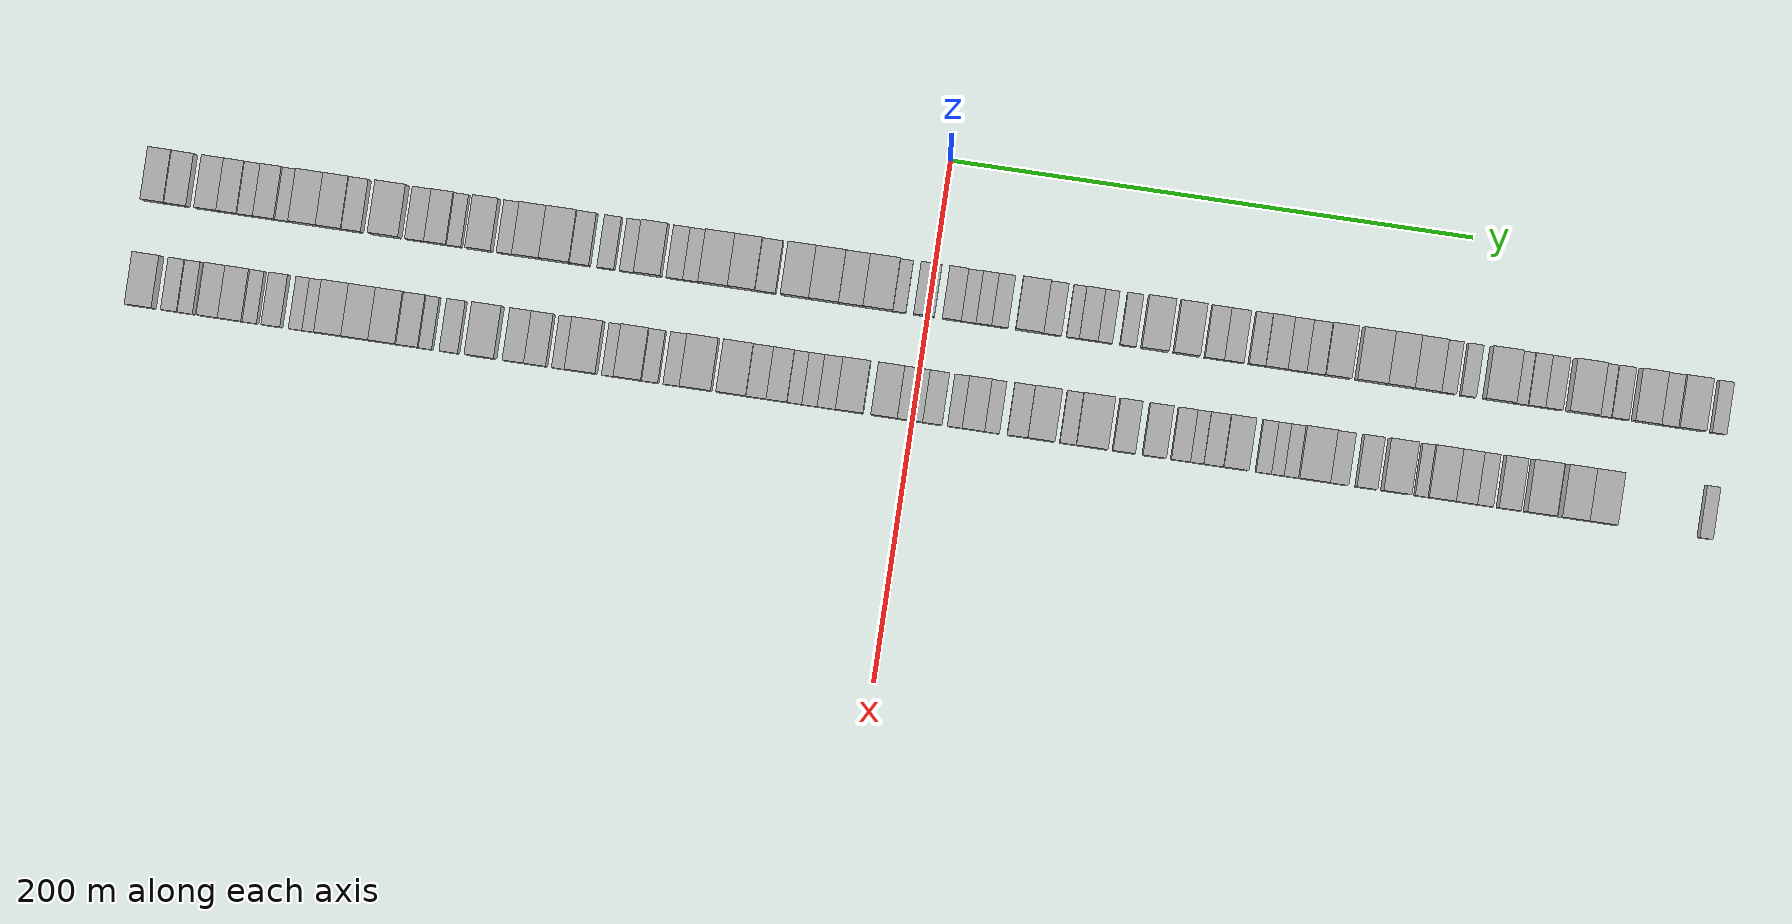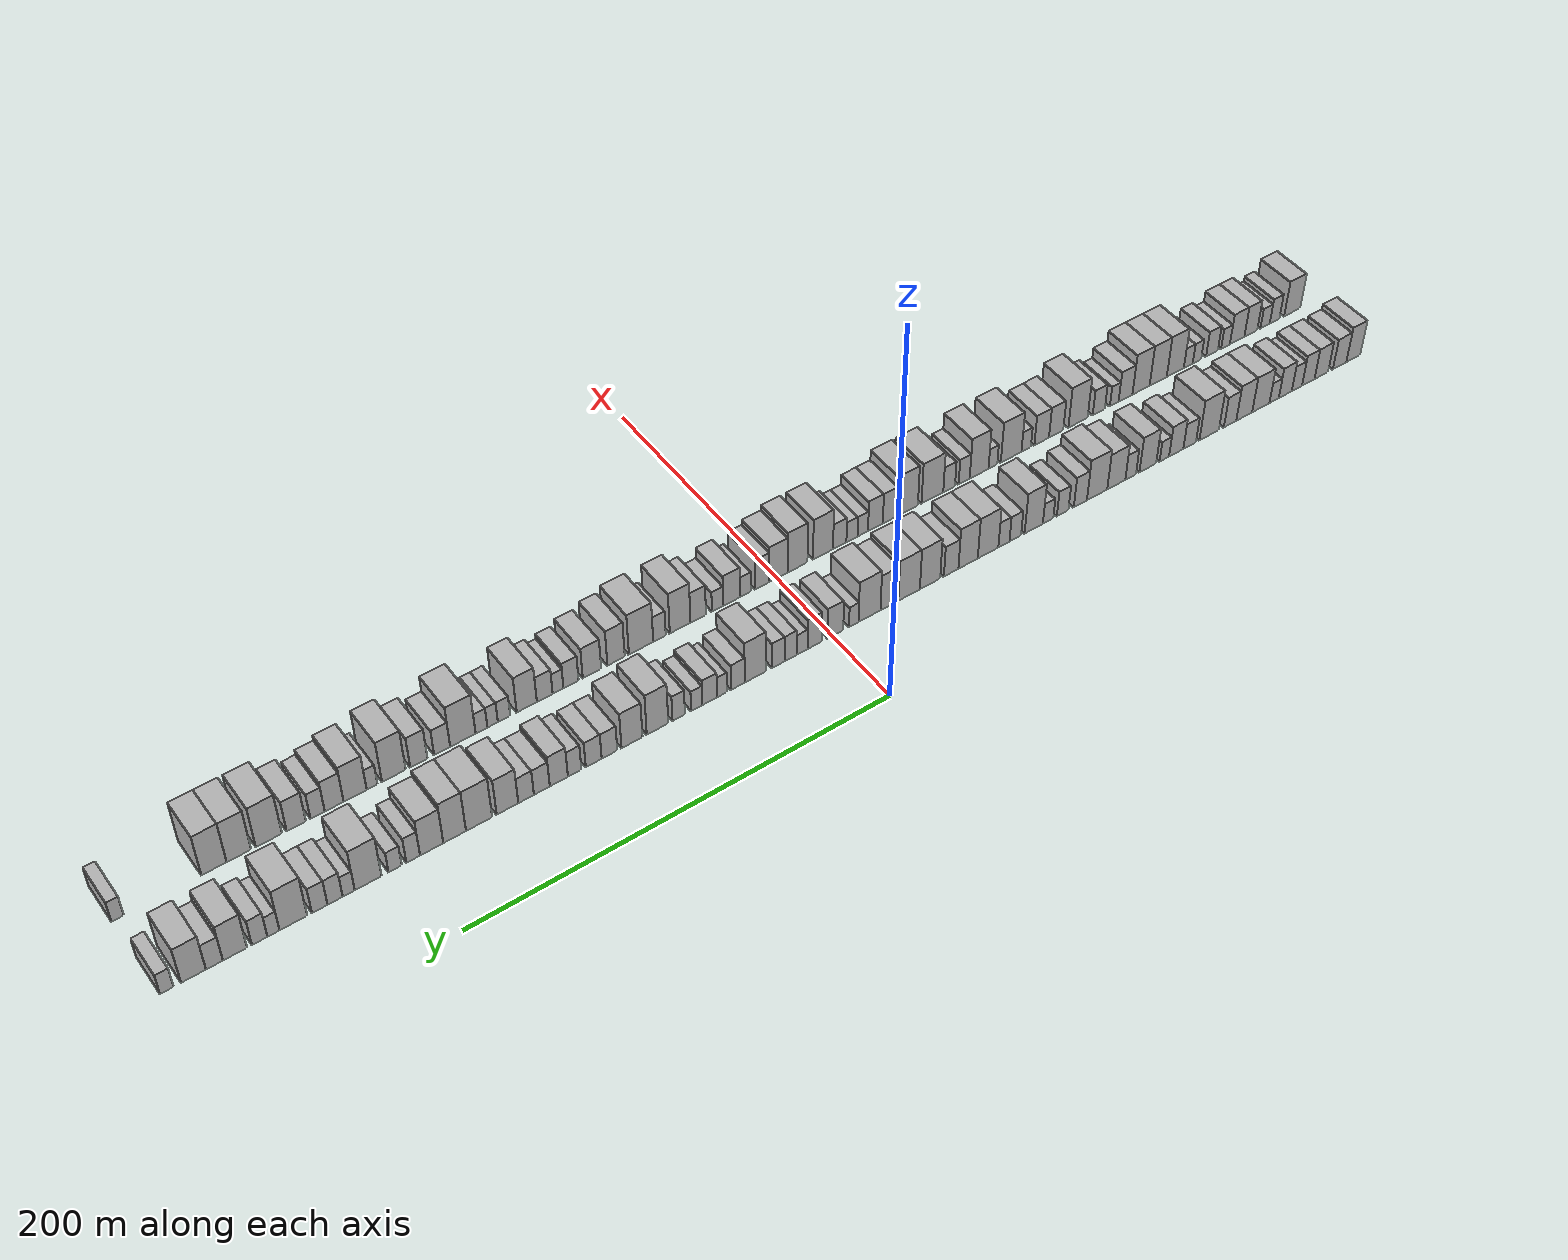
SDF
<sdf version="1.6">
 <world name="default">
  <scene>
   <sky><clouds><speed>12</speed></clouds></sky>
   <ambient>0.4 0.4 0.4 1</ambient>
   <background>0.7 0.7 0.7 1</background>
   <shadows>1</shadows>
  </scene>
  <gravity>0 0 -9.8066</gravity>
  <magnetic_field>6e-06 2.3e-05 -4.2e-05</magnetic_field>
  <physics default="0" name="default_physics" type="ode">
   <ode>
    <solver>
     <type>quick</type>
     <iters>10</iters>
     <sor>1.0</sor>
     <use_dynamic_moi_rescaling>0</use_dynamic_moi_rescaling>
    </solver>
    <constraints>
     <cfm>0</cfm>
     <erp>0.2</erp>
     <contact_max_correcting_vel>100</contact_max_correcting_vel>
     <contact_surface_layer>0.001</contact_surface_layer>
    </constraints>
   </ode>
   <max_step_size>0.004</max_step_size>
   <real_time_factor>1</real_time_factor>
   <real_time_update_rate>250</real_time_update_rate>
  </physics>
  <light name="sun" type="directional">
   <pose>0 0 10 0 0 0</pose>
   <diffuse>0.8 0.8 0.8 1</diffuse>
   <specular>0.2 0.2 0.2 1</specular>
   <attenuation>
    <range>1000</range>
    <constant>0.9</constant>
    <linear>0.01</linear>
    <quadratic>0.001</quadratic>
   </attenuation>
   <direction>-0.5 0.1 -0.9</direction>
  </light>
  <model name="building_1">
   <static>1</static>
   <pose>50.0000 -295.6084 0 0.000000 0.000000 0.000000</pose>
   <link name="link">
    <pose>0 0 10.50 0 0 0</pose>
    <collision name="collision"><geometry><box><size>20.0000 8.7832 21.0000</size></box></geometry></collision>
    <visual name="visual">
     <cast_shadows>0</cast_shadows>
     <geometry><box><size>20.0000 8.7832 21.0000</size></box></geometry>
     <material>
      <script>
       <uri>model://HANNAS_wall/materials/scripts</uri>
       <uri>model://HANNAS_wall/materials/textures</uri>
       <name>vrc/HANNAS_wall</name>
      </script>
     </material>
    </visual>
   </link>
  </model>
  <model name="building_2">
   <static>1</static>
   <pose>50.0000 -287.0106 0 0.000000 0.000000 0.000000</pose>
   <link name="link">
    <pose>0 0 9.00 0 0 0</pose>
    <collision name="collision"><geometry><box><size>20.0000 8.4124 18.0000</size></box></geometry></collision>
    <visual name="visual">
     <cast_shadows>0</cast_shadows>
     <geometry><box><size>20.0000 8.4124 18.0000</size></box></geometry>
     <material>
      <script>
       <uri>model://HANNAS_wall/materials/scripts</uri>
       <uri>model://HANNAS_wall/materials/textures</uri>
       <name>vrc/HANNAS_wall</name>
      </script>
     </material>
    </visual>
   </link>
  </model>
  <model name="building_3">
   <static>1</static>
   <pose>50.0000 -275.5951 0 0.000000 0.000000 0.000000</pose>
   <link name="link">
    <pose>0 0 9.00 0 0 0</pose>
    <collision name="collision"><geometry><box><size>20.0000 8.4186 18.0000</size></box></geometry></collision>
    <visual name="visual">
     <cast_shadows>0</cast_shadows>
     <geometry><box><size>20.0000 8.4186 18.0000</size></box></geometry>
     <material>
      <script>
       <uri>model://HANNAS_wall/materials/scripts</uri>
       <uri>model://HANNAS_wall/materials/textures</uri>
       <name>vrc/HANNAS_wall</name>
      </script>
     </material>
    </visual>
   </link>
  </model>
  <model name="building_4">
   <static>1</static>
   <pose>50.0000 -267.5192 0 0.000000 0.000000 0.000000</pose>
   <link name="link">
    <pose>0 0 9.00 0 0 0</pose>
    <collision name="collision"><geometry><box><size>20.0000 7.7331 18.0000</size></box></geometry></collision>
    <visual name="visual">
     <cast_shadows>0</cast_shadows>
     <geometry><box><size>20.0000 7.7331 18.0000</size></box></geometry>
     <material>
      <script>
       <uri>model://HANNAS_wall/materials/scripts</uri>
       <uri>model://HANNAS_wall/materials/textures</uri>
       <name>vrc/HANNAS_wall</name>
      </script>
     </material>
    </visual>
   </link>
  </model>
  <model name="building_5">
   <static>1</static>
   <pose>50.0000 -260.5304 0 0.000000 0.000000 0.000000</pose>
   <link name="link">
    <pose>0 0 7.50 0 0 0</pose>
    <collision name="collision"><geometry><box><size>20.0000 6.2446 15.0000</size></box></geometry></collision>
    <visual name="visual">
     <cast_shadows>0</cast_shadows>
     <geometry><box><size>20.0000 6.2446 15.0000</size></box></geometry>
     <material>
      <script>
       <uri>model://HANNAS_wall/materials/scripts</uri>
       <uri>model://HANNAS_wall/materials/textures</uri>
       <name>vrc/HANNAS_wall</name>
      </script>
     </material>
    </visual>
   </link>
  </model>
  <model name="building_6">
   <static>1</static>
   <pose>50.0000 -253.3990 0 0.000000 0.000000 0.000000</pose>
   <link name="link">
    <pose>0 0 9.00 0 0 0</pose>
    <collision name="collision"><geometry><box><size>20.0000 8.0182 18.0000</size></box></geometry></collision>
    <visual name="visual">
     <cast_shadows>0</cast_shadows>
     <geometry><box><size>20.0000 8.0182 18.0000</size></box></geometry>
     <material>
      <script>
       <uri>model://HANNAS_wall/materials/scripts</uri>
       <uri>model://HANNAS_wall/materials/textures</uri>
       <name>vrc/HANNAS_wall</name>
      </script>
     </material>
    </visual>
   </link>
  </model>
  <model name="building_7">
   <static>1</static>
   <pose>50.0000 -246.5467 0 0.000000 0.000000 0.000000</pose>
   <link name="link">
    <pose>0 0 6.00 0 0 0</pose>
    <collision name="collision"><geometry><box><size>20.0000 5.6864 12.0000</size></box></geometry></collision>
    <visual name="visual">
     <cast_shadows>0</cast_shadows>
     <geometry><box><size>20.0000 5.6864 12.0000</size></box></geometry>
     <material>
      <script>
       <uri>model://HANNAS_wall/materials/scripts</uri>
       <uri>model://HANNAS_wall/materials/textures</uri>
       <name>vrc/HANNAS_wall</name>
      </script>
     </material>
    </visual>
   </link>
  </model>
  <model name="building_8">
   <static>1</static>
   <pose>50.0000 -238.4841 0 0.000000 0.000000 0.000000</pose>
   <link name="link">
    <pose>0 0 10.50 0 0 0</pose>
    <collision name="collision"><geometry><box><size>20.0000 10.4387 21.0000</size></box></geometry></collision>
    <visual name="visual">
     <cast_shadows>0</cast_shadows>
     <geometry><box><size>20.0000 10.4387 21.0000</size></box></geometry>
     <material>
      <script>
       <uri>model://HANNAS_wall/materials/scripts</uri>
       <uri>model://HANNAS_wall/materials/textures</uri>
       <name>vrc/HANNAS_wall</name>
      </script>
     </material>
    </visual>
   </link>
  </model>
  <model name="building_9">
   <static>1</static>
   <pose>50.0000 -228.4582 0 0.000000 0.000000 0.000000</pose>
   <link name="link">
    <pose>0 0 10.50 0 0 0</pose>
    <collision name="collision"><geometry><box><size>20.0000 9.6133 21.0000</size></box></geometry></collision>
    <visual name="visual">
     <cast_shadows>0</cast_shadows>
     <geometry><box><size>20.0000 9.6133 21.0000</size></box></geometry>
     <material>
      <script>
       <uri>model://HANNAS_wall/materials/scripts</uri>
       <uri>model://HANNAS_wall/materials/textures</uri>
       <name>vrc/HANNAS_wall</name>
      </script>
     </material>
    </visual>
   </link>
  </model>
  <model name="building_10">
   <static>1</static>
   <pose>50.0000 -219.9443 0 0.000000 0.000000 0.000000</pose>
   <link name="link">
    <pose>0 0 9.00 0 0 0</pose>
    <collision name="collision"><geometry><box><size>20.0000 7.4143 18.0000</size></box></geometry></collision>
    <visual name="visual">
     <cast_shadows>0</cast_shadows>
     <geometry><box><size>20.0000 7.4143 18.0000</size></box></geometry>
     <material>
      <script>
       <uri>model://HANNAS_wall/materials/scripts</uri>
       <uri>model://HANNAS_wall/materials/textures</uri>
       <name>vrc/HANNAS_wall</name>
      </script>
     </material>
    </visual>
   </link>
  </model>
  <model name="building_11">
   <static>1</static>
   <pose>50.0000 -207.4244 0 0.000000 0.000000 0.000000</pose>
   <link name="link">
    <pose>0 0 12.00 0 0 0</pose>
    <collision name="collision"><geometry><box><size>20.0000 11.6256 24.0000</size></box></geometry></collision>
    <visual name="visual">
     <cast_shadows>0</cast_shadows>
     <geometry><box><size>20.0000 11.6256 24.0000</size></box></geometry>
     <material>
      <script>
       <uri>model://HANNAS_wall/materials/scripts</uri>
       <uri>model://HANNAS_wall/materials/textures</uri>
       <name>vrc/HANNAS_wall</name>
      </script>
     </material>
    </visual>
   </link>
  </model>
  <model name="building_12">
   <static>1</static>
   <pose>50.0000 -195.9075 0 0.000000 0.000000 0.000000</pose>
   <link name="link">
    <pose>0 0 7.50 0 0 0</pose>
    <collision name="collision"><geometry><box><size>20.0000 7.4081 15.0000</size></box></geometry></collision>
    <visual name="visual">
     <cast_shadows>0</cast_shadows>
     <geometry><box><size>20.0000 7.4081 15.0000</size></box></geometry>
     <material>
      <script>
       <uri>model://HANNAS_wall/materials/scripts</uri>
       <uri>model://HANNAS_wall/materials/textures</uri>
       <name>vrc/HANNAS_wall</name>
      </script>
     </material>
    </visual>
   </link>
  </model>
  <model name="building_13">
   <static>1</static>
   <pose>50.0000 -188.0218 0 0.000000 0.000000 0.000000</pose>
   <link name="link">
    <pose>0 0 9.00 0 0 0</pose>
    <collision name="collision"><geometry><box><size>20.0000 8.3633 18.0000</size></box></geometry></collision>
    <visual name="visual">
     <cast_shadows>0</cast_shadows>
     <geometry><box><size>20.0000 8.3633 18.0000</size></box></geometry>
     <material>
      <script>
       <uri>model://HANNAS_wall/materials/scripts</uri>
       <uri>model://HANNAS_wall/materials/textures</uri>
       <name>vrc/HANNAS_wall</name>
      </script>
     </material>
    </visual>
   </link>
  </model>
  <model name="building_14">
   <static>1</static>
   <pose>50.0000 -181.0776 0 0.000000 0.000000 0.000000</pose>
   <link name="link">
    <pose>0 0 6.00 0 0 0</pose>
    <collision name="collision"><geometry><box><size>20.0000 5.5251 12.0000</size></box></geometry></collision>
    <visual name="visual">
     <cast_shadows>0</cast_shadows>
     <geometry><box><size>20.0000 5.5251 12.0000</size></box></geometry>
     <material>
      <script>
       <uri>model://HANNAS_wall/materials/scripts</uri>
       <uri>model://HANNAS_wall/materials/textures</uri>
       <name>vrc/HANNAS_wall</name>
      </script>
     </material>
    </visual>
   </link>
  </model>
  <model name="building_15">
   <static>1</static>
   <pose>50.0000 -171.4688 0 0.000000 0.000000 0.000000</pose>
   <link name="link">
    <pose>0 0 10.50 0 0 0</pose>
    <collision name="collision"><geometry><box><size>20.0000 9.6924 21.0000</size></box></geometry></collision>
    <visual name="visual">
     <cast_shadows>0</cast_shadows>
     <geometry><box><size>20.0000 9.6924 21.0000</size></box></geometry>
     <material>
      <script>
       <uri>model://HANNAS_wall/materials/scripts</uri>
       <uri>model://HANNAS_wall/materials/textures</uri>
       <name>vrc/HANNAS_wall</name>
      </script>
     </material>
    </visual>
   </link>
  </model>
  <model name="building_16">
   <static>1</static>
   <pose>50.0000 -161.5749 0 0.000000 0.000000 0.000000</pose>
   <link name="link">
    <pose>0 0 7.50 0 0 0</pose>
    <collision name="collision"><geometry><box><size>20.0000 6.0954 15.0000</size></box></geometry></collision>
    <visual name="visual">
     <cast_shadows>0</cast_shadows>
     <geometry><box><size>20.0000 6.0954 15.0000</size></box></geometry>
     <material>
      <script>
       <uri>model://HANNAS_wall/materials/scripts</uri>
       <uri>model://HANNAS_wall/materials/textures</uri>
       <name>vrc/HANNAS_wall</name>
      </script>
     </material>
    </visual>
   </link>
  </model>
  <model name="building_17">
   <static>1</static>
   <pose>50.0000 -153.3585 0 0.000000 0.000000 0.000000</pose>
   <link name="link">
    <pose>0 0 10.50 0 0 0</pose>
    <collision name="collision"><geometry><box><size>20.0000 10.3374 21.0000</size></box></geometry></collision>
    <visual name="visual">
     <cast_shadows>0</cast_shadows>
     <geometry><box><size>20.0000 10.3374 21.0000</size></box></geometry>
     <material>
      <script>
       <uri>model://HANNAS_wall/materials/scripts</uri>
       <uri>model://HANNAS_wall/materials/textures</uri>
       <name>vrc/HANNAS_wall</name>
      </script>
     </material>
    </visual>
   </link>
  </model>
  <model name="building_18">
   <static>1</static>
   <pose>50.0000 -142.4200 0 0.000000 0.000000 0.000000</pose>
   <link name="link">
    <pose>0 0 12.00 0 0 0</pose>
    <collision name="collision"><geometry><box><size>20.0000 11.5396 24.0000</size></box></geometry></collision>
    <visual name="visual">
     <cast_shadows>0</cast_shadows>
     <geometry><box><size>20.0000 11.5396 24.0000</size></box></geometry>
     <material>
      <script>
       <uri>model://HANNAS_wall/materials/scripts</uri>
       <uri>model://HANNAS_wall/materials/textures</uri>
       <name>vrc/HANNAS_wall</name>
      </script>
     </material>
    </visual>
   </link>
  </model>
  <model name="building_19">
   <static>1</static>
   <pose>50.0000 -132.9575 0 0.000000 0.000000 0.000000</pose>
   <link name="link">
    <pose>0 0 9.00 0 0 0</pose>
    <collision name="collision"><geometry><box><size>20.0000 7.3854 18.0000</size></box></geometry></collision>
    <visual name="visual">
     <cast_shadows>0</cast_shadows>
     <geometry><box><size>20.0000 7.3854 18.0000</size></box></geometry>
     <material>
      <script>
       <uri>model://HANNAS_wall/materials/scripts</uri>
       <uri>model://HANNAS_wall/materials/textures</uri>
       <name>vrc/HANNAS_wall</name>
      </script>
     </material>
    </visual>
   </link>
  </model>
  <model name="building_20">
   <static>1</static>
   <pose>50.0000 -123.0354 0 0.000000 0.000000 0.000000</pose>
   <link name="link">
    <pose>0 0 7.50 0 0 0</pose>
    <collision name="collision"><geometry><box><size>20.0000 6.4587 15.0000</size></box></geometry></collision>
    <visual name="visual">
     <cast_shadows>0</cast_shadows>
     <geometry><box><size>20.0000 6.4587 15.0000</size></box></geometry>
     <material>
      <script>
       <uri>model://HANNAS_wall/materials/scripts</uri>
       <uri>model://HANNAS_wall/materials/textures</uri>
       <name>vrc/HANNAS_wall</name>
      </script>
     </material>
    </visual>
   </link>
  </model>
  <model name="building_21">
   <static>1</static>
   <pose>50.0000 -114.9029 0 0.000000 0.000000 0.000000</pose>
   <link name="link">
    <pose>0 0 6.00 0 0 0</pose>
    <collision name="collision"><geometry><box><size>20.0000 5.8064 12.0000</size></box></geometry></collision>
    <visual name="visual">
     <cast_shadows>0</cast_shadows>
     <geometry><box><size>20.0000 5.8064 12.0000</size></box></geometry>
     <material>
      <script>
       <uri>model://HANNAS_wall/materials/scripts</uri>
       <uri>model://HANNAS_wall/materials/textures</uri>
       <name>vrc/HANNAS_wall</name>
      </script>
     </material>
    </visual>
   </link>
  </model>
  <model name="building_22">
   <static>1</static>
   <pose>50.0000 -106.9604 0 0.000000 0.000000 0.000000</pose>
   <link name="link">
    <pose>0 0 12.00 0 0 0</pose>
    <collision name="collision"><geometry><box><size>20.0000 10.0785 24.0000</size></box></geometry></collision>
    <visual name="visual">
     <cast_shadows>0</cast_shadows>
     <geometry><box><size>20.0000 10.0785 24.0000</size></box></geometry>
     <material>
      <script>
       <uri>model://HANNAS_wall/materials/scripts</uri>
       <uri>model://HANNAS_wall/materials/textures</uri>
       <name>vrc/HANNAS_wall</name>
      </script>
     </material>
    </visual>
   </link>
  </model>
  <model name="building_23">
   <static>1</static>
   <pose>50.0000 -96.7455 0 0.000000 0.000000 0.000000</pose>
   <link name="link">
    <pose>0 0 7.50 0 0 0</pose>
    <collision name="collision"><geometry><box><size>20.0000 6.3514 15.0000</size></box></geometry></collision>
    <visual name="visual">
     <cast_shadows>0</cast_shadows>
     <geometry><box><size>20.0000 6.3514 15.0000</size></box></geometry>
     <material>
      <script>
       <uri>model://HANNAS_wall/materials/scripts</uri>
       <uri>model://HANNAS_wall/materials/textures</uri>
       <name>vrc/HANNAS_wall</name>
      </script>
     </material>
    </visual>
   </link>
  </model>
  <model name="building_24">
   <static>1</static>
   <pose>50.0000 -90.5376 0 0.000000 0.000000 0.000000</pose>
   <link name="link">
    <pose>0 0 7.50 0 0 0</pose>
    <collision name="collision"><geometry><box><size>20.0000 6.0643 15.0000</size></box></geometry></collision>
    <visual name="visual">
     <cast_shadows>0</cast_shadows>
     <geometry><box><size>20.0000 6.0643 15.0000</size></box></geometry>
     <material>
      <script>
       <uri>model://HANNAS_wall/materials/scripts</uri>
       <uri>model://HANNAS_wall/materials/textures</uri>
       <name>vrc/HANNAS_wall</name>
      </script>
     </material>
    </visual>
   </link>
  </model>
  <model name="building_25">
   <static>1</static>
   <pose>50.0000 -81.9061 0 0.000000 0.000000 0.000000</pose>
   <link name="link">
    <pose>0 0 12.00 0 0 0</pose>
    <collision name="collision"><geometry><box><size>20.0000 11.1988 24.0000</size></box></geometry></collision>
    <visual name="visual">
     <cast_shadows>0</cast_shadows>
     <geometry><box><size>20.0000 11.1988 24.0000</size></box></geometry>
     <material>
      <script>
       <uri>model://HANNAS_wall/materials/scripts</uri>
       <uri>model://HANNAS_wall/materials/textures</uri>
       <name>vrc/HANNAS_wall</name>
      </script>
     </material>
    </visual>
   </link>
  </model>
  <model name="building_26">
   <static>1</static>
   <pose>50.0000 -71.0972 0 0.000000 0.000000 0.000000</pose>
   <link name="link">
    <pose>0 0 12.00 0 0 0</pose>
    <collision name="collision"><geometry><box><size>20.0000 10.4188 24.0000</size></box></geometry></collision>
    <visual name="visual">
     <cast_shadows>0</cast_shadows>
     <geometry><box><size>20.0000 10.4188 24.0000</size></box></geometry>
     <material>
      <script>
       <uri>model://HANNAS_wall/materials/scripts</uri>
       <uri>model://HANNAS_wall/materials/textures</uri>
       <name>vrc/HANNAS_wall</name>
      </script>
     </material>
    </visual>
   </link>
  </model>
  <model name="building_27">
   <static>1</static>
   <pose>50.0000 -62.0028 0 0.000000 0.000000 0.000000</pose>
   <link name="link">
    <pose>0 0 9.00 0 0 0</pose>
    <collision name="collision"><geometry><box><size>20.0000 7.7700 18.0000</size></box></geometry></collision>
    <visual name="visual">
     <cast_shadows>0</cast_shadows>
     <geometry><box><size>20.0000 7.7700 18.0000</size></box></geometry>
     <material>
      <script>
       <uri>model://HANNAS_wall/materials/scripts</uri>
       <uri>model://HANNAS_wall/materials/textures</uri>
       <name>vrc/HANNAS_wall</name>
      </script>
     </material>
    </visual>
   </link>
  </model>
  <model name="building_28">
   <static>1</static>
   <pose>50.0000 -50.7396 0 0.000000 0.000000 0.000000</pose>
   <link name="link">
    <pose>0 0 12.00 0 0 0</pose>
    <collision name="collision"><geometry><box><size>20.0000 10.7563 24.0000</size></box></geometry></collision>
    <visual name="visual">
     <cast_shadows>0</cast_shadows>
     <geometry><box><size>20.0000 10.7563 24.0000</size></box></geometry>
     <material>
      <script>
       <uri>model://HANNAS_wall/materials/scripts</uri>
       <uri>model://HANNAS_wall/materials/textures</uri>
       <name>vrc/HANNAS_wall</name>
      </script>
     </material>
    </visual>
   </link>
  </model>
  <model name="building_29">
   <static>1</static>
   <pose>50.0000 -39.6867 0 0.000000 0.000000 0.000000</pose>
   <link name="link">
    <pose>0 0 12.00 0 0 0</pose>
    <collision name="collision"><geometry><box><size>20.0000 11.3496 24.0000</size></box></geometry></collision>
    <visual name="visual">
     <cast_shadows>0</cast_shadows>
     <geometry><box><size>20.0000 11.3496 24.0000</size></box></geometry>
     <material>
      <script>
       <uri>model://HANNAS_wall/materials/scripts</uri>
       <uri>model://HANNAS_wall/materials/textures</uri>
       <name>vrc/HANNAS_wall</name>
      </script>
     </material>
    </visual>
   </link>
  </model>
  <model name="building_30">
   <static>1</static>
   <pose>50.0000 -29.3589 0 0.000000 0.000000 0.000000</pose>
   <link name="link">
    <pose>0 0 10.50 0 0 0</pose>
    <collision name="collision"><geometry><box><size>20.0000 9.3060 21.0000</size></box></geometry></collision>
    <visual name="visual">
     <cast_shadows>0</cast_shadows>
     <geometry><box><size>20.0000 9.3060 21.0000</size></box></geometry>
     <material>
      <script>
       <uri>model://HANNAS_wall/materials/scripts</uri>
       <uri>model://HANNAS_wall/materials/textures</uri>
       <name>vrc/HANNAS_wall</name>
      </script>
     </material>
    </visual>
   </link>
  </model>
  <model name="building_31">
   <static>1</static>
   <pose>50.0000 -19.0063 0 0.000000 0.000000 0.000000</pose>
   <link name="link">
    <pose>0 0 12.00 0 0 0</pose>
    <collision name="collision"><geometry><box><size>20.0000 11.3990 24.0000</size></box></geometry></collision>
    <visual name="visual">
     <cast_shadows>0</cast_shadows>
     <geometry><box><size>20.0000 11.3990 24.0000</size></box></geometry>
     <material>
      <script>
       <uri>model://HANNAS_wall/materials/scripts</uri>
       <uri>model://HANNAS_wall/materials/textures</uri>
       <name>vrc/HANNAS_wall</name>
      </script>
     </material>
    </visual>
   </link>
  </model>
  <model name="building_32">
   <static>1</static>
   <pose>50.0000 -10.8610 0 0.000000 0.000000 0.000000</pose>
   <link name="link">
    <pose>0 0 6.00 0 0 0</pose>
    <collision name="collision"><geometry><box><size>20.0000 4.8917 12.0000</size></box></geometry></collision>
    <visual name="visual">
     <cast_shadows>0</cast_shadows>
     <geometry><box><size>20.0000 4.8917 12.0000</size></box></geometry>
     <material>
      <script>
       <uri>model://HANNAS_wall/materials/scripts</uri>
       <uri>model://HANNAS_wall/materials/textures</uri>
       <name>vrc/HANNAS_wall</name>
      </script>
     </material>
    </visual>
   </link>
  </model>
  <model name="building_33">
   <static>1</static>
   <pose>50.0000 -1.4541 0 0.000000 0.000000 0.000000</pose>
   <link name="link">
    <pose>0 0 9.00 0 0 0</pose>
    <collision name="collision"><geometry><box><size>20.0000 7.9220 18.0000</size></box></geometry></collision>
    <visual name="visual">
     <cast_shadows>0</cast_shadows>
     <geometry><box><size>20.0000 7.9220 18.0000</size></box></geometry>
     <material>
      <script>
       <uri>model://HANNAS_wall/materials/scripts</uri>
       <uri>model://HANNAS_wall/materials/textures</uri>
       <name>vrc/HANNAS_wall</name>
      </script>
     </material>
    </visual>
   </link>
  </model>
  <model name="building_34">
   <static>1</static>
   <pose>50.0000 9.1386 0 0.000000 0.000000 0.000000</pose>
   <link name="link">
    <pose>0 0 9.00 0 0 0</pose>
    <collision name="collision"><geometry><box><size>20.0000 7.2633 18.0000</size></box></geometry></collision>
    <visual name="visual">
     <cast_shadows>0</cast_shadows>
     <geometry><box><size>20.0000 7.2633 18.0000</size></box></geometry>
     <material>
      <script>
       <uri>model://HANNAS_wall/materials/scripts</uri>
       <uri>model://HANNAS_wall/materials/textures</uri>
       <name>vrc/HANNAS_wall</name>
      </script>
     </material>
    </visual>
   </link>
  </model>
  <model name="building_35">
   <static>1</static>
   <pose>50.0000 15.5627 0 0.000000 0.000000 0.000000</pose>
   <link name="link">
    <pose>0 0 6.00 0 0 0</pose>
    <collision name="collision"><geometry><box><size>20.0000 5.5849 12.0000</size></box></geometry></collision>
    <visual name="visual">
     <cast_shadows>0</cast_shadows>
     <geometry><box><size>20.0000 5.5849 12.0000</size></box></geometry>
     <material>
      <script>
       <uri>model://HANNAS_wall/materials/scripts</uri>
       <uri>model://HANNAS_wall/materials/textures</uri>
       <name>vrc/HANNAS_wall</name>
      </script>
     </material>
    </visual>
   </link>
  </model>
  <model name="building_36">
   <static>1</static>
   <pose>50.0000 21.3634 0 0.000000 0.000000 0.000000</pose>
   <link name="link">
    <pose>0 0 7.50 0 0 0</pose>
    <collision name="collision"><geometry><box><size>20.0000 6.0165 15.0000</size></box></geometry></collision>
    <visual name="visual">
     <cast_shadows>0</cast_shadows>
     <geometry><box><size>20.0000 6.0165 15.0000</size></box></geometry>
     <material>
      <script>
       <uri>model://HANNAS_wall/materials/scripts</uri>
       <uri>model://HANNAS_wall/materials/textures</uri>
       <name>vrc/HANNAS_wall</name>
      </script>
     </material>
    </visual>
   </link>
  </model>
  <model name="building_37">
   <static>1</static>
   <pose>50.0000 27.4844 0 0.000000 0.000000 0.000000</pose>
   <link name="link">
    <pose>0 0 7.50 0 0 0</pose>
    <collision name="collision"><geometry><box><size>20.0000 6.2254 15.0000</size></box></geometry></collision>
    <visual name="visual">
     <cast_shadows>0</cast_shadows>
     <geometry><box><size>20.0000 6.2254 15.0000</size></box></geometry>
     <material>
      <script>
       <uri>model://HANNAS_wall/materials/scripts</uri>
       <uri>model://HANNAS_wall/materials/textures</uri>
       <name>vrc/HANNAS_wall</name>
      </script>
     </material>
    </visual>
   </link>
  </model>
  <model name="building_38">
   <static>1</static>
   <pose>50.0000 38.8776 0 0.000000 0.000000 0.000000</pose>
   <link name="link">
    <pose>0 0 12.00 0 0 0</pose>
    <collision name="collision"><geometry><box><size>20.0000 10.5609 24.0000</size></box></geometry></collision>
    <visual name="visual">
     <cast_shadows>0</cast_shadows>
     <geometry><box><size>20.0000 10.5609 24.0000</size></box></geometry>
     <material>
      <script>
       <uri>model://HANNAS_wall/materials/scripts</uri>
       <uri>model://HANNAS_wall/materials/textures</uri>
       <name>vrc/HANNAS_wall</name>
      </script>
     </material>
    </visual>
   </link>
  </model>
  <model name="building_39">
   <static>1</static>
   <pose>50.0000 47.5717 0 0.000000 0.000000 0.000000</pose>
   <link name="link">
    <pose>0 0 7.50 0 0 0</pose>
    <collision name="collision"><geometry><box><size>20.0000 6.8272 15.0000</size></box></geometry></collision>
    <visual name="visual">
     <cast_shadows>0</cast_shadows>
     <geometry><box><size>20.0000 6.8272 15.0000</size></box></geometry>
     <material>
      <script>
       <uri>model://HANNAS_wall/materials/scripts</uri>
       <uri>model://HANNAS_wall/materials/textures</uri>
       <name>vrc/HANNAS_wall</name>
      </script>
     </material>
    </visual>
   </link>
  </model>
  <model name="building_40">
   <static>1</static>
   <pose>50.0000 55.4066 0 0.000000 0.000000 0.000000</pose>
   <link name="link">
    <pose>0 0 6.00 0 0 0</pose>
    <collision name="collision"><geometry><box><size>20.0000 4.8426 12.0000</size></box></geometry></collision>
    <visual name="visual">
     <cast_shadows>0</cast_shadows>
     <geometry><box><size>20.0000 4.8426 12.0000</size></box></geometry>
     <material>
      <script>
       <uri>model://HANNAS_wall/materials/scripts</uri>
       <uri>model://HANNAS_wall/materials/textures</uri>
       <name>vrc/HANNAS_wall</name>
      </script>
     </material>
    </visual>
   </link>
  </model>
  <model name="building_41">
   <static>1</static>
   <pose>50.0000 61.4080 0 0.000000 0.000000 0.000000</pose>
   <link name="link">
    <pose>0 0 7.50 0 0 0</pose>
    <collision name="collision"><geometry><box><size>20.0000 7.1603 15.0000</size></box></geometry></collision>
    <visual name="visual">
     <cast_shadows>0</cast_shadows>
     <geometry><box><size>20.0000 7.1603 15.0000</size></box></geometry>
     <material>
      <script>
       <uri>model://HANNAS_wall/materials/scripts</uri>
       <uri>model://HANNAS_wall/materials/textures</uri>
       <name>vrc/HANNAS_wall</name>
      </script>
     </material>
    </visual>
   </link>
  </model>
  <model name="building_42">
   <static>1</static>
   <pose>50.0000 67.7312 0 0.000000 0.000000 0.000000</pose>
   <link name="link">
    <pose>0 0 6.00 0 0 0</pose>
    <collision name="collision"><geometry><box><size>20.0000 5.4860 12.0000</size></box></geometry></collision>
    <visual name="visual">
     <cast_shadows>0</cast_shadows>
     <geometry><box><size>20.0000 5.4860 12.0000</size></box></geometry>
     <material>
      <script>
       <uri>model://HANNAS_wall/materials/scripts</uri>
       <uri>model://HANNAS_wall/materials/textures</uri>
       <name>vrc/HANNAS_wall</name>
      </script>
     </material>
    </visual>
   </link>
  </model>
  <model name="building_43">
   <static>1</static>
   <pose>50.0000 76.4869 0 0.000000 0.000000 0.000000</pose>
   <link name="link">
    <pose>0 0 7.50 0 0 0</pose>
    <collision name="collision"><geometry><box><size>20.0000 6.0255 15.0000</size></box></geometry></collision>
    <visual name="visual">
     <cast_shadows>0</cast_shadows>
     <geometry><box><size>20.0000 6.0255 15.0000</size></box></geometry>
     <material>
      <script>
       <uri>model://HANNAS_wall/materials/scripts</uri>
       <uri>model://HANNAS_wall/materials/textures</uri>
       <name>vrc/HANNAS_wall</name>
      </script>
     </material>
    </visual>
   </link>
  </model>
  <model name="building_44">
   <static>1</static>
   <pose>50.0000 86.6789 0 0.000000 0.000000 0.000000</pose>
   <link name="link">
    <pose>0 0 12.00 0 0 0</pose>
    <collision name="collision"><geometry><box><size>20.0000 10.3585 24.0000</size></box></geometry></collision>
    <visual name="visual">
     <cast_shadows>0</cast_shadows>
     <geometry><box><size>20.0000 10.3585 24.0000</size></box></geometry>
     <material>
      <script>
       <uri>model://HANNAS_wall/materials/scripts</uri>
       <uri>model://HANNAS_wall/materials/textures</uri>
       <name>vrc/HANNAS_wall</name>
      </script>
     </material>
    </visual>
   </link>
  </model>
  <model name="building_45">
   <static>1</static>
   <pose>50.0000 98.8367 0 0.000000 0.000000 0.000000</pose>
   <link name="link">
    <pose>0 0 10.50 0 0 0</pose>
    <collision name="collision"><geometry><box><size>20.0000 9.9571 21.0000</size></box></geometry></collision>
    <visual name="visual">
     <cast_shadows>0</cast_shadows>
     <geometry><box><size>20.0000 9.9571 21.0000</size></box></geometry>
     <material>
      <script>
       <uri>model://HANNAS_wall/materials/scripts</uri>
       <uri>model://HANNAS_wall/materials/textures</uri>
       <name>vrc/HANNAS_wall</name>
      </script>
     </material>
    </visual>
   </link>
  </model>
  <model name="building_46">
   <static>1</static>
   <pose>50.0000 109.4958 0 0.000000 0.000000 0.000000</pose>
   <link name="link">
    <pose>0 0 7.50 0 0 0</pose>
    <collision name="collision"><geometry><box><size>20.0000 7.3610 15.0000</size></box></geometry></collision>
    <visual name="visual">
     <cast_shadows>0</cast_shadows>
     <geometry><box><size>20.0000 7.3610 15.0000</size></box></geometry>
     <material>
      <script>
       <uri>model://HANNAS_wall/materials/scripts</uri>
       <uri>model://HANNAS_wall/materials/textures</uri>
       <name>vrc/HANNAS_wall</name>
      </script>
     </material>
    </visual>
   </link>
  </model>
  <model name="building_47">
   <static>1</static>
   <pose>50.0000 116.9033 0 0.000000 0.000000 0.000000</pose>
   <link name="link">
    <pose>0 0 7.50 0 0 0</pose>
    <collision name="collision"><geometry><box><size>20.0000 7.4541 15.0000</size></box></geometry></collision>
    <visual name="visual">
     <cast_shadows>0</cast_shadows>
     <geometry><box><size>20.0000 7.4541 15.0000</size></box></geometry>
     <material>
      <script>
       <uri>model://HANNAS_wall/materials/scripts</uri>
       <uri>model://HANNAS_wall/materials/textures</uri>
       <name>vrc/HANNAS_wall</name>
      </script>
     </material>
    </visual>
   </link>
  </model>
  <model name="building_48">
   <static>1</static>
   <pose>50.0000 125.7696 0 0.000000 0.000000 0.000000</pose>
   <link name="link">
    <pose>0 0 7.50 0 0 0</pose>
    <collision name="collision"><geometry><box><size>20.0000 6.2784 15.0000</size></box></geometry></collision>
    <visual name="visual">
     <cast_shadows>0</cast_shadows>
     <geometry><box><size>20.0000 6.2784 15.0000</size></box></geometry>
     <material>
      <script>
       <uri>model://HANNAS_wall/materials/scripts</uri>
       <uri>model://HANNAS_wall/materials/textures</uri>
       <name>vrc/HANNAS_wall</name>
      </script>
     </material>
    </visual>
   </link>
  </model>
  <model name="building_49">
   <static>1</static>
   <pose>50.0000 133.0935 0 0.000000 0.000000 0.000000</pose>
   <link name="link">
    <pose>0 0 9.00 0 0 0</pose>
    <collision name="collision"><geometry><box><size>20.0000 8.3695 18.0000</size></box></geometry></collision>
    <visual name="visual">
     <cast_shadows>0</cast_shadows>
     <geometry><box><size>20.0000 8.3695 18.0000</size></box></geometry>
     <material>
      <script>
       <uri>model://HANNAS_wall/materials/scripts</uri>
       <uri>model://HANNAS_wall/materials/textures</uri>
       <name>vrc/HANNAS_wall</name>
      </script>
     </material>
    </visual>
   </link>
  </model>
  <model name="building_50">
   <static>1</static>
   <pose>50.0000 140.9272 0 0.000000 0.000000 0.000000</pose>
   <link name="link">
    <pose>0 0 7.50 0 0 0</pose>
    <collision name="collision"><geometry><box><size>20.0000 7.2979 15.0000</size></box></geometry></collision>
    <visual name="visual">
     <cast_shadows>0</cast_shadows>
     <geometry><box><size>20.0000 7.2979 15.0000</size></box></geometry>
     <material>
      <script>
       <uri>model://HANNAS_wall/materials/scripts</uri>
       <uri>model://HANNAS_wall/materials/textures</uri>
       <name>vrc/HANNAS_wall</name>
      </script>
     </material>
    </visual>
   </link>
  </model>
  <model name="building_51">
   <static>1</static>
   <pose>50.0000 148.1332 0 0.000000 0.000000 0.000000</pose>
   <link name="link">
    <pose>0 0 7.50 0 0 0</pose>
    <collision name="collision"><geometry><box><size>20.0000 7.1141 15.0000</size></box></geometry></collision>
    <visual name="visual">
     <cast_shadows>0</cast_shadows>
     <geometry><box><size>20.0000 7.1141 15.0000</size></box></geometry>
     <material>
      <script>
       <uri>model://HANNAS_wall/materials/scripts</uri>
       <uri>model://HANNAS_wall/materials/textures</uri>
       <name>vrc/HANNAS_wall</name>
      </script>
     </material>
    </visual>
   </link>
  </model>
  <model name="building_52">
   <static>1</static>
   <pose>50.0000 156.6143 0 0.000000 0.000000 0.000000</pose>
   <link name="link">
    <pose>0 0 10.50 0 0 0</pose>
    <collision name="collision"><geometry><box><size>20.0000 9.8481 21.0000</size></box></geometry></collision>
    <visual name="visual">
     <cast_shadows>0</cast_shadows>
     <geometry><box><size>20.0000 9.8481 21.0000</size></box></geometry>
     <material>
      <script>
       <uri>model://HANNAS_wall/materials/scripts</uri>
       <uri>model://HANNAS_wall/materials/textures</uri>
       <name>vrc/HANNAS_wall</name>
      </script>
     </material>
    </visual>
   </link>
  </model>
  <model name="building_53">
   <static>1</static>
   <pose>50.0000 169.4247 0 0.000000 0.000000 0.000000</pose>
   <link name="link">
    <pose>0 0 12.00 0 0 0</pose>
    <collision name="collision"><geometry><box><size>20.0000 11.7728 24.0000</size></box></geometry></collision>
    <visual name="visual">
     <cast_shadows>0</cast_shadows>
     <geometry><box><size>20.0000 11.7728 24.0000</size></box></geometry>
     <material>
      <script>
       <uri>model://HANNAS_wall/materials/scripts</uri>
       <uri>model://HANNAS_wall/materials/textures</uri>
       <name>vrc/HANNAS_wall</name>
      </script>
     </material>
    </visual>
   </link>
  </model>
  <model name="building_54">
   <static>1</static>
   <pose>50.0000 180.3538 0 0.000000 0.000000 0.000000</pose>
   <link name="link">
    <pose>0 0 12.00 0 0 0</pose>
    <collision name="collision"><geometry><box><size>20.0000 10.0854 24.0000</size></box></geometry></collision>
    <visual name="visual">
     <cast_shadows>0</cast_shadows>
     <geometry><box><size>20.0000 10.0854 24.0000</size></box></geometry>
     <material>
      <script>
       <uri>model://HANNAS_wall/materials/scripts</uri>
       <uri>model://HANNAS_wall/materials/textures</uri>
       <name>vrc/HANNAS_wall</name>
      </script>
     </material>
    </visual>
   </link>
  </model>
  <model name="building_55">
   <static>1</static>
   <pose>50.0000 190.5391 0 0.000000 0.000000 0.000000</pose>
   <link name="link">
    <pose>0 0 10.50 0 0 0</pose>
    <collision name="collision"><geometry><box><size>20.0000 10.2852 21.0000</size></box></geometry></collision>
    <visual name="visual">
     <cast_shadows>0</cast_shadows>
     <geometry><box><size>20.0000 10.2852 21.0000</size></box></geometry>
     <material>
      <script>
       <uri>model://HANNAS_wall/materials/scripts</uri>
       <uri>model://HANNAS_wall/materials/textures</uri>
       <name>vrc/HANNAS_wall</name>
      </script>
     </material>
    </visual>
   </link>
  </model>
  <model name="building_56">
   <static>1</static>
   <pose>50.0000 198.6832 0 0.000000 0.000000 0.000000</pose>
   <link name="link">
    <pose>0 0 7.50 0 0 0</pose>
    <collision name="collision"><geometry><box><size>20.0000 6.0030 15.0000</size></box></geometry></collision>
    <visual name="visual">
     <cast_shadows>0</cast_shadows>
     <geometry><box><size>20.0000 6.0030 15.0000</size></box></geometry>
     <material>
      <script>
       <uri>model://HANNAS_wall/materials/scripts</uri>
       <uri>model://HANNAS_wall/materials/textures</uri>
       <name>vrc/HANNAS_wall</name>
      </script>
     </material>
    </visual>
   </link>
  </model>
  <model name="building_57">
   <static>1</static>
   <pose>50.0000 206.5739 0 0.000000 0.000000 0.000000</pose>
   <link name="link">
    <pose>0 0 6.00 0 0 0</pose>
    <collision name="collision"><geometry><box><size>20.0000 5.7784 12.0000</size></box></geometry></collision>
    <visual name="visual">
     <cast_shadows>0</cast_shadows>
     <geometry><box><size>20.0000 5.7784 12.0000</size></box></geometry>
     <material>
      <script>
       <uri>model://HANNAS_wall/materials/scripts</uri>
       <uri>model://HANNAS_wall/materials/textures</uri>
       <name>vrc/HANNAS_wall</name>
      </script>
     </material>
    </visual>
   </link>
  </model>
  <model name="building_58">
   <static>1</static>
   <pose>50.0000 218.2641 0 0.000000 0.000000 0.000000</pose>
   <link name="link">
    <pose>0 0 12.00 0 0 0</pose>
    <collision name="collision"><geometry><box><size>20.0000 11.6019 24.0000</size></box></geometry></collision>
    <visual name="visual">
     <cast_shadows>0</cast_shadows>
     <geometry><box><size>20.0000 11.6019 24.0000</size></box></geometry>
     <material>
      <script>
       <uri>model://HANNAS_wall/materials/scripts</uri>
       <uri>model://HANNAS_wall/materials/textures</uri>
       <name>vrc/HANNAS_wall</name>
      </script>
     </material>
    </visual>
   </link>
  </model>
  <model name="building_59">
   <static>1</static>
   <pose>50.0000 226.6419 0 0.000000 0.000000 0.000000</pose>
   <link name="link">
    <pose>0 0 6.00 0 0 0</pose>
    <collision name="collision"><geometry><box><size>20.0000 5.1538 12.0000</size></box></geometry></collision>
    <visual name="visual">
     <cast_shadows>0</cast_shadows>
     <geometry><box><size>20.0000 5.1538 12.0000</size></box></geometry>
     <material>
      <script>
       <uri>model://HANNAS_wall/materials/scripts</uri>
       <uri>model://HANNAS_wall/materials/textures</uri>
       <name>vrc/HANNAS_wall</name>
      </script>
     </material>
    </visual>
   </link>
  </model>
  <model name="building_60">
   <static>1</static>
   <pose>50.0000 232.4467 0 0.000000 0.000000 0.000000</pose>
   <link name="link">
    <pose>0 0 7.50 0 0 0</pose>
    <collision name="collision"><geometry><box><size>20.0000 6.4557 15.0000</size></box></geometry></collision>
    <visual name="visual">
     <cast_shadows>0</cast_shadows>
     <geometry><box><size>20.0000 6.4557 15.0000</size></box></geometry>
     <material>
      <script>
       <uri>model://HANNAS_wall/materials/scripts</uri>
       <uri>model://HANNAS_wall/materials/textures</uri>
       <name>vrc/HANNAS_wall</name>
      </script>
     </material>
    </visual>
   </link>
  </model>
  <model name="building_61">
   <static>1</static>
   <pose>50.0000 238.9981 0 0.000000 0.000000 0.000000</pose>
   <link name="link">
    <pose>0 0 7.50 0 0 0</pose>
    <collision name="collision"><geometry><box><size>20.0000 6.6470 15.0000</size></box></geometry></collision>
    <visual name="visual">
     <cast_shadows>0</cast_shadows>
     <geometry><box><size>20.0000 6.6470 15.0000</size></box></geometry>
     <material>
      <script>
       <uri>model://HANNAS_wall/materials/scripts</uri>
       <uri>model://HANNAS_wall/materials/textures</uri>
       <name>vrc/HANNAS_wall</name>
      </script>
     </material>
    </visual>
   </link>
  </model>
  <model name="building_62">
   <static>1</static>
   <pose>50.0000 250.1455 0 0.000000 0.000000 0.000000</pose>
   <link name="link">
    <pose>0 0 12.00 0 0 0</pose>
    <collision name="collision"><geometry><box><size>20.0000 11.6477 24.0000</size></box></geometry></collision>
    <visual name="visual">
     <cast_shadows>0</cast_shadows>
     <geometry><box><size>20.0000 11.6477 24.0000</size></box></geometry>
     <material>
      <script>
       <uri>model://HANNAS_wall/materials/scripts</uri>
       <uri>model://HANNAS_wall/materials/textures</uri>
       <name>vrc/HANNAS_wall</name>
      </script>
     </material>
    </visual>
   </link>
  </model>
  <model name="building_63">
   <static>1</static>
   <pose>50.0000 258.4861 0 0.000000 0.000000 0.000000</pose>
   <link name="link">
    <pose>0 0 6.00 0 0 0</pose>
    <collision name="collision"><geometry><box><size>20.0000 5.0337 12.0000</size></box></geometry></collision>
    <visual name="visual">
     <cast_shadows>0</cast_shadows>
     <geometry><box><size>20.0000 5.0337 12.0000</size></box></geometry>
     <material>
      <script>
       <uri>model://HANNAS_wall/materials/scripts</uri>
       <uri>model://HANNAS_wall/materials/textures</uri>
       <name>vrc/HANNAS_wall</name>
      </script>
     </material>
    </visual>
   </link>
  </model>
  <model name="building_64">
   <static>1</static>
   <pose>50.0000 264.2400 0 0.000000 0.000000 0.000000</pose>
   <link name="link">
    <pose>0 0 7.50 0 0 0</pose>
    <collision name="collision"><geometry><box><size>20.0000 6.4740 15.0000</size></box></geometry></collision>
    <visual name="visual">
     <cast_shadows>0</cast_shadows>
     <geometry><box><size>20.0000 6.4740 15.0000</size></box></geometry>
     <material>
      <script>
       <uri>model://HANNAS_wall/materials/scripts</uri>
       <uri>model://HANNAS_wall/materials/textures</uri>
       <name>vrc/HANNAS_wall</name>
      </script>
     </material>
    </visual>
   </link>
  </model>
  <model name="building_65">
   <static>1</static>
   <pose>50.0000 274.4589 0 0.000000 0.000000 0.000000</pose>
   <link name="link">
    <pose>0 0 10.50 0 0 0</pose>
    <collision name="collision"><geometry><box><size>20.0000 9.9638 21.0000</size></box></geometry></collision>
    <visual name="visual">
     <cast_shadows>0</cast_shadows>
     <geometry><box><size>20.0000 9.9638 21.0000</size></box></geometry>
     <material>
      <script>
       <uri>model://HANNAS_wall/materials/scripts</uri>
       <uri>model://HANNAS_wall/materials/textures</uri>
       <name>vrc/HANNAS_wall</name>
      </script>
     </material>
    </visual>
   </link>
  </model>
  <model name="building_66">
   <static>1</static>
   <pose>50.0000 282.9145 0 0.000000 0.000000 0.000000</pose>
   <link name="link">
    <pose>0 0 7.50 0 0 0</pose>
    <collision name="collision"><geometry><box><size>20.0000 6.9473 15.0000</size></box></geometry></collision>
    <visual name="visual">
     <cast_shadows>0</cast_shadows>
     <geometry><box><size>20.0000 6.9473 15.0000</size></box></geometry>
     <material>
      <script>
       <uri>model://HANNAS_wall/materials/scripts</uri>
       <uri>model://HANNAS_wall/materials/textures</uri>
       <name>vrc/HANNAS_wall</name>
      </script>
     </material>
    </visual>
   </link>
  </model>
  <model name="building_67">
   <static>1</static>
   <pose>50.0000 291.4581 0 0.000000 0.000000 0.000000</pose>
   <link name="link">
    <pose>0 0 10.50 0 0 0</pose>
    <collision name="collision"><geometry><box><size>20.0000 10.1399 21.0000</size></box></geometry></collision>
    <visual name="visual">
     <cast_shadows>0</cast_shadows>
     <geometry><box><size>20.0000 10.1399 21.0000</size></box></geometry>
     <material>
      <script>
       <uri>model://HANNAS_wall/materials/scripts</uri>
       <uri>model://HANNAS_wall/materials/textures</uri>
       <name>vrc/HANNAS_wall</name>
      </script>
     </material>
    </visual>
   </link>
  </model>
  <model name="building_68">
   <static>1</static>
   <pose>50.0000 302.2902 0 0.000000 0.000000 0.000000</pose>
   <link name="link">
    <pose>0 0 6.00 0 0 0</pose>
    <collision name="collision"><geometry><box><size>20.0000 5.5241 12.0000</size></box></geometry></collision>
    <visual name="visual">
     <cast_shadows>0</cast_shadows>
     <geometry><box><size>20.0000 5.5241 12.0000</size></box></geometry>
     <material>
      <script>
       <uri>model://HANNAS_wall/materials/scripts</uri>
       <uri>model://HANNAS_wall/materials/textures</uri>
       <name>vrc/HANNAS_wall</name>
      </script>
     </material>
    </visual>
   </link>
  </model>
  <model name="building_69">
   <static>1</static>
   <pose>90.0000 -294.8831 0 0.000000 0.000000 0.000000</pose>
   <link name="link">
    <pose>0 0 10.50 0 0 0</pose>
    <collision name="collision"><geometry><box><size>20.0000 10.2337 21.0000</size></box></geometry></collision>
    <visual name="visual">
     <cast_shadows>0</cast_shadows>
     <geometry><box><size>20.0000 10.2337 21.0000</size></box></geometry>
     <material>
      <script>
       <uri>model://HANNAS_wall/materials/scripts</uri>
       <uri>model://HANNAS_wall/materials/textures</uri>
       <name>vrc/HANNAS_wall</name>
      </script>
     </material>
    </visual>
   </link>
  </model>
  <model name="building_70">
   <static>1</static>
   <pose>90.0000 -283.7280 0 0.000000 0.000000 0.000000</pose>
   <link name="link">
    <pose>0 0 7.50 0 0 0</pose>
    <collision name="collision"><geometry><box><size>20.0000 6.0766 15.0000</size></box></geometry></collision>
    <visual name="visual">
     <cast_shadows>0</cast_shadows>
     <geometry><box><size>20.0000 6.0766 15.0000</size></box></geometry>
     <material>
      <script>
       <uri>model://HANNAS_wall/materials/scripts</uri>
       <uri>model://HANNAS_wall/materials/textures</uri>
       <name>vrc/HANNAS_wall</name>
      </script>
     </material>
    </visual>
   </link>
  </model>
  <model name="building_71">
   <static>1</static>
   <pose>90.0000 -277.7828 0 0.000000 0.000000 0.000000</pose>
   <link name="link">
    <pose>0 0 6.00 0 0 0</pose>
    <collision name="collision"><geometry><box><size>20.0000 5.8138 12.0000</size></box></geometry></collision>
    <visual name="visual">
     <cast_shadows>0</cast_shadows>
     <geometry><box><size>20.0000 5.8138 12.0000</size></box></geometry>
     <material>
      <script>
       <uri>model://HANNAS_wall/materials/scripts</uri>
       <uri>model://HANNAS_wall/materials/textures</uri>
       <name>vrc/HANNAS_wall</name>
      </script>
     </material>
    </visual>
   </link>
  </model>
  <model name="building_72">
   <static>1</static>
   <pose>90.0000 -268.8610 0 0.000000 0.000000 0.000000</pose>
   <link name="link">
    <pose>0 0 9.00 0 0 0</pose>
    <collision name="collision"><geometry><box><size>20.0000 8.0298 18.0000</size></box></geometry></collision>
    <visual name="visual">
     <cast_shadows>0</cast_shadows>
     <geometry><box><size>20.0000 8.0298 18.0000</size></box></geometry>
     <material>
      <script>
       <uri>model://HANNAS_wall/materials/scripts</uri>
       <uri>model://HANNAS_wall/materials/textures</uri>
       <name>vrc/HANNAS_wall</name>
      </script>
     </material>
    </visual>
   </link>
  </model>
  <model name="building_73">
   <static>1</static>
   <pose>90.0000 -260.3591 0 0.000000 0.000000 0.000000</pose>
   <link name="link">
    <pose>0 0 9.00 0 0 0</pose>
    <collision name="collision"><geometry><box><size>20.0000 8.9741 18.0000</size></box></geometry></collision>
    <visual name="visual">
     <cast_shadows>0</cast_shadows>
     <geometry><box><size>20.0000 8.9741 18.0000</size></box></geometry>
     <material>
      <script>
       <uri>model://HANNAS_wall/materials/scripts</uri>
       <uri>model://HANNAS_wall/materials/textures</uri>
       <name>vrc/HANNAS_wall</name>
      </script>
     </material>
    </visual>
   </link>
  </model>
  <model name="building_74">
   <static>1</static>
   <pose>90.0000 -253.1556 0 0.000000 0.000000 0.000000</pose>
   <link name="link">
    <pose>0 0 6.00 0 0 0</pose>
    <collision name="collision"><geometry><box><size>20.0000 5.4329 12.0000</size></box></geometry></collision>
    <visual name="visual">
     <cast_shadows>0</cast_shadows>
     <geometry><box><size>20.0000 5.4329 12.0000</size></box></geometry>
     <material>
      <script>
       <uri>model://HANNAS_wall/materials/scripts</uri>
       <uri>model://HANNAS_wall/materials/textures</uri>
       <name>vrc/HANNAS_wall</name>
      </script>
     </material>
    </visual>
   </link>
  </model>
  <model name="building_75">
   <static>1</static>
   <pose>90.0000 -244.8351 0 0.000000 0.000000 0.000000</pose>
   <link name="link">
    <pose>0 0 7.50 0 0 0</pose>
    <collision name="collision"><geometry><box><size>20.0000 7.2080 15.0000</size></box></geometry></collision>
    <visual name="visual">
     <cast_shadows>0</cast_shadows>
     <geometry><box><size>20.0000 7.2080 15.0000</size></box></geometry>
     <material>
      <script>
       <uri>model://HANNAS_wall/materials/scripts</uri>
       <uri>model://HANNAS_wall/materials/textures</uri>
       <name>vrc/HANNAS_wall</name>
      </script>
     </material>
    </visual>
   </link>
  </model>
  <model name="building_76">
   <static>1</static>
   <pose>90.0000 -235.6593 0 0.000000 0.000000 0.000000</pose>
   <link name="link">
    <pose>0 0 6.00 0 0 0</pose>
    <collision name="collision"><geometry><box><size>20.0000 5.1436 12.0000</size></box></geometry></collision>
    <visual name="visual">
     <cast_shadows>0</cast_shadows>
     <geometry><box><size>20.0000 5.1436 12.0000</size></box></geometry>
     <material>
      <script>
       <uri>model://HANNAS_wall/materials/scripts</uri>
       <uri>model://HANNAS_wall/materials/textures</uri>
       <name>vrc/HANNAS_wall</name>
      </script>
     </material>
    </visual>
   </link>
  </model>
  <model name="building_77">
   <static>1</static>
   <pose>90.0000 -230.3656 0 0.000000 0.000000 0.000000</pose>
   <link name="link">
    <pose>0 0 6.00 0 0 0</pose>
    <collision name="collision"><geometry><box><size>20.0000 5.4438 12.0000</size></box></geometry></collision>
    <visual name="visual">
     <cast_shadows>0</cast_shadows>
     <geometry><box><size>20.0000 5.4438 12.0000</size></box></geometry>
     <material>
      <script>
       <uri>model://HANNAS_wall/materials/scripts</uri>
       <uri>model://HANNAS_wall/materials/textures</uri>
       <name>vrc/HANNAS_wall</name>
      </script>
     </material>
    </visual>
   </link>
  </model>
  <model name="building_78">
   <static>1</static>
   <pose>90.0000 -222.4977 0 0.000000 0.000000 0.000000</pose>
   <link name="link">
    <pose>0 0 12.00 0 0 0</pose>
    <collision name="collision"><geometry><box><size>20.0000 10.2920 24.0000</size></box></geometry></collision>
    <visual name="visual">
     <cast_shadows>0</cast_shadows>
     <geometry><box><size>20.0000 10.2920 24.0000</size></box></geometry>
     <material>
      <script>
       <uri>model://HANNAS_wall/materials/scripts</uri>
       <uri>model://HANNAS_wall/materials/textures</uri>
       <name>vrc/HANNAS_wall</name>
      </script>
     </material>
    </visual>
   </link>
  </model>
  <model name="building_79">
   <static>1</static>
   <pose>90.0000 -212.2177 0 0.000000 0.000000 0.000000</pose>
   <link name="link">
    <pose>0 0 12.00 0 0 0</pose>
    <collision name="collision"><geometry><box><size>20.0000 10.2680 24.0000</size></box></geometry></collision>
    <visual name="visual">
     <cast_shadows>0</cast_shadows>
     <geometry><box><size>20.0000 10.2680 24.0000</size></box></geometry>
     <material>
      <script>
       <uri>model://HANNAS_wall/materials/scripts</uri>
       <uri>model://HANNAS_wall/materials/textures</uri>
       <name>vrc/HANNAS_wall</name>
      </script>
     </material>
    </visual>
   </link>
  </model>
  <model name="building_80">
   <static>1</static>
   <pose>90.0000 -201.9517 0 0.000000 0.000000 0.000000</pose>
   <link name="link">
    <pose>0 0 12.00 0 0 0</pose>
    <collision name="collision"><geometry><box><size>20.0000 10.2640 24.0000</size></box></geometry></collision>
    <visual name="visual">
     <cast_shadows>0</cast_shadows>
     <geometry><box><size>20.0000 10.2640 24.0000</size></box></geometry>
     <material>
      <script>
       <uri>model://HANNAS_wall/materials/scripts</uri>
       <uri>model://HANNAS_wall/materials/textures</uri>
       <name>vrc/HANNAS_wall</name>
      </script>
     </material>
    </visual>
   </link>
  </model>
  <model name="building_81">
   <static>1</static>
   <pose>90.0000 -192.7112 0 0.000000 0.000000 0.000000</pose>
   <link name="link">
    <pose>0 0 9.00 0 0 0</pose>
    <collision name="collision"><geometry><box><size>20.0000 8.2171 18.0000</size></box></geometry></collision>
    <visual name="visual">
     <cast_shadows>0</cast_shadows>
     <geometry><box><size>20.0000 8.2171 18.0000</size></box></geometry>
     <material>
      <script>
       <uri>model://HANNAS_wall/materials/scripts</uri>
       <uri>model://HANNAS_wall/materials/textures</uri>
       <name>vrc/HANNAS_wall</name>
      </script>
     </material>
    </visual>
   </link>
  </model>
  <model name="building_82">
   <static>1</static>
   <pose>90.0000 -186.0684 0 0.000000 0.000000 0.000000</pose>
   <link name="link">
    <pose>0 0 6.00 0 0 0</pose>
    <collision name="collision"><geometry><box><size>20.0000 5.0684 12.0000</size></box></geometry></collision>
    <visual name="visual">
     <cast_shadows>0</cast_shadows>
     <geometry><box><size>20.0000 5.0684 12.0000</size></box></geometry>
     <material>
      <script>
       <uri>model://HANNAS_wall/materials/scripts</uri>
       <uri>model://HANNAS_wall/materials/textures</uri>
       <name>vrc/HANNAS_wall</name>
      </script>
     </material>
    </visual>
   </link>
  </model>
  <model name="building_83">
   <static>1</static>
   <pose>90.0000 -176.9957 0 0.000000 0.000000 0.000000</pose>
   <link name="link">
    <pose>0 0 7.50 0 0 0</pose>
    <collision name="collision"><geometry><box><size>20.0000 7.0769 15.0000</size></box></geometry></collision>
    <visual name="visual">
     <cast_shadows>0</cast_shadows>
     <geometry><box><size>20.0000 7.0769 15.0000</size></box></geometry>
     <material>
      <script>
       <uri>model://HANNAS_wall/materials/scripts</uri>
       <uri>model://HANNAS_wall/materials/textures</uri>
       <name>vrc/HANNAS_wall</name>
      </script>
     </material>
    </visual>
   </link>
  </model>
  <model name="building_84">
   <static>1</static>
   <pose>90.0000 -164.8664 0 0.000000 0.000000 0.000000</pose>
   <link name="link">
    <pose>0 0 12.00 0 0 0</pose>
    <collision name="collision"><geometry><box><size>20.0000 11.1818 24.0000</size></box></geometry></collision>
    <visual name="visual">
     <cast_shadows>0</cast_shadows>
     <geometry><box><size>20.0000 11.1818 24.0000</size></box></geometry>
     <material>
      <script>
       <uri>model://HANNAS_wall/materials/scripts</uri>
       <uri>model://HANNAS_wall/materials/textures</uri>
       <name>vrc/HANNAS_wall</name>
      </script>
     </material>
    </visual>
   </link>
  </model>
  <model name="building_85">
   <static>1</static>
   <pose>90.0000 -152.1957 0 0.000000 0.000000 0.000000</pose>
   <link name="link">
    <pose>0 0 9.00 0 0 0</pose>
    <collision name="collision"><geometry><box><size>20.0000 8.1596 18.0000</size></box></geometry></collision>
    <visual name="visual">
     <cast_shadows>0</cast_shadows>
     <geometry><box><size>20.0000 8.1596 18.0000</size></box></geometry>
     <material>
      <script>
       <uri>model://HANNAS_wall/materials/scripts</uri>
       <uri>model://HANNAS_wall/materials/textures</uri>
       <name>vrc/HANNAS_wall</name>
      </script>
     </material>
    </visual>
   </link>
  </model>
  <model name="building_86">
   <static>1</static>
   <pose>90.0000 -143.9330 0 0.000000 0.000000 0.000000</pose>
   <link name="link">
    <pose>0 0 9.00 0 0 0</pose>
    <collision name="collision"><geometry><box><size>20.0000 8.3658 18.0000</size></box></geometry></collision>
    <visual name="visual">
     <cast_shadows>0</cast_shadows>
     <geometry><box><size>20.0000 8.3658 18.0000</size></box></geometry>
     <material>
      <script>
       <uri>model://HANNAS_wall/materials/scripts</uri>
       <uri>model://HANNAS_wall/materials/textures</uri>
       <name>vrc/HANNAS_wall</name>
      </script>
     </material>
    </visual>
   </link>
  </model>
  <model name="building_87">
   <static>1</static>
   <pose>90.0000 -135.0626 0 0.000000 0.000000 0.000000</pose>
   <link name="link">
    <pose>0 0 6.00 0 0 0</pose>
    <collision name="collision"><geometry><box><size>20.0000 5.3749 12.0000</size></box></geometry></collision>
    <visual name="visual">
     <cast_shadows>0</cast_shadows>
     <geometry><box><size>20.0000 5.3749 12.0000</size></box></geometry>
     <material>
      <script>
       <uri>model://HANNAS_wall/materials/scripts</uri>
       <uri>model://HANNAS_wall/materials/textures</uri>
       <name>vrc/HANNAS_wall</name>
      </script>
     </material>
    </visual>
   </link>
  </model>
  <model name="building_88">
   <static>1</static>
   <pose>90.0000 -126.5322 0 0.000000 0.000000 0.000000</pose>
   <link name="link">
    <pose>0 0 12.00 0 0 0</pose>
    <collision name="collision"><geometry><box><size>20.0000 11.6860 24.0000</size></box></geometry></collision>
    <visual name="visual">
     <cast_shadows>0</cast_shadows>
     <geometry><box><size>20.0000 11.6860 24.0000</size></box></geometry>
     <material>
      <script>
       <uri>model://HANNAS_wall/materials/scripts</uri>
       <uri>model://HANNAS_wall/materials/textures</uri>
       <name>vrc/HANNAS_wall</name>
      </script>
     </material>
    </visual>
   </link>
  </model>
  <model name="building_89">
   <static>1</static>
   <pose>90.0000 -116.2276 0 0.000000 0.000000 0.000000</pose>
   <link name="link">
    <pose>0 0 6.00 0 0 0</pose>
    <collision name="collision"><geometry><box><size>20.0000 4.9231 12.0000</size></box></geometry></collision>
    <visual name="visual">
     <cast_shadows>0</cast_shadows>
     <geometry><box><size>20.0000 4.9231 12.0000</size></box></geometry>
     <material>
      <script>
       <uri>model://HANNAS_wall/materials/scripts</uri>
       <uri>model://HANNAS_wall/materials/textures</uri>
       <name>vrc/HANNAS_wall</name>
      </script>
     </material>
    </visual>
   </link>
  </model>
  <model name="building_90">
   <static>1</static>
   <pose>90.0000 -108.5277 0 0.000000 0.000000 0.000000</pose>
   <link name="link">
    <pose>0 0 12.00 0 0 0</pose>
    <collision name="collision"><geometry><box><size>20.0000 10.4768 24.0000</size></box></geometry></collision>
    <visual name="visual">
     <cast_shadows>0</cast_shadows>
     <geometry><box><size>20.0000 10.4768 24.0000</size></box></geometry>
     <material>
      <script>
       <uri>model://HANNAS_wall/materials/scripts</uri>
       <uri>model://HANNAS_wall/materials/textures</uri>
       <name>vrc/HANNAS_wall</name>
      </script>
     </material>
    </visual>
   </link>
  </model>
  <model name="building_91">
   <static>1</static>
   <pose>90.0000 -100.1976 0 0.000000 0.000000 0.000000</pose>
   <link name="link">
    <pose>0 0 7.50 0 0 0</pose>
    <collision name="collision"><geometry><box><size>20.0000 6.1833 15.0000</size></box></geometry></collision>
    <visual name="visual">
     <cast_shadows>0</cast_shadows>
     <geometry><box><size>20.0000 6.1833 15.0000</size></box></geometry>
     <material>
      <script>
       <uri>model://HANNAS_wall/materials/scripts</uri>
       <uri>model://HANNAS_wall/materials/textures</uri>
       <name>vrc/HANNAS_wall</name>
      </script>
     </material>
    </visual>
   </link>
  </model>
  <model name="building_92">
   <static>1</static>
   <pose>90.0000 -91.8778 0 0.000000 0.000000 0.000000</pose>
   <link name="link">
    <pose>0 0 7.50 0 0 0</pose>
    <collision name="collision"><geometry><box><size>20.0000 6.4563 15.0000</size></box></geometry></collision>
    <visual name="visual">
     <cast_shadows>0</cast_shadows>
     <geometry><box><size>20.0000 6.4563 15.0000</size></box></geometry>
     <material>
      <script>
       <uri>model://HANNAS_wall/materials/scripts</uri>
       <uri>model://HANNAS_wall/materials/textures</uri>
       <name>vrc/HANNAS_wall</name>
      </script>
     </material>
    </visual>
   </link>
  </model>
  <model name="building_93">
   <static>1</static>
   <pose>90.0000 -82.6861 0 0.000000 0.000000 0.000000</pose>
   <link name="link">
    <pose>0 0 12.00 0 0 0</pose>
    <collision name="collision"><geometry><box><size>20.0000 11.9272 24.0000</size></box></geometry></collision>
    <visual name="visual">
     <cast_shadows>0</cast_shadows>
     <geometry><box><size>20.0000 11.9272 24.0000</size></box></geometry>
     <material>
      <script>
       <uri>model://HANNAS_wall/materials/scripts</uri>
       <uri>model://HANNAS_wall/materials/textures</uri>
       <name>vrc/HANNAS_wall</name>
      </script>
     </material>
    </visual>
   </link>
  </model>
  <model name="building_94">
   <static>1</static>
   <pose>90.0000 -69.0409 0 0.000000 0.000000 0.000000</pose>
   <link name="link">
    <pose>0 0 12.00 0 0 0</pose>
    <collision name="collision"><geometry><box><size>20.0000 11.3632 24.0000</size></box></geometry></collision>
    <visual name="visual">
     <cast_shadows>0</cast_shadows>
     <geometry><box><size>20.0000 11.3632 24.0000</size></box></geometry>
     <material>
      <script>
       <uri>model://HANNAS_wall/materials/scripts</uri>
       <uri>model://HANNAS_wall/materials/textures</uri>
       <name>vrc/HANNAS_wall</name>
      </script>
     </material>
    </visual>
   </link>
  </model>
  <model name="building_95">
   <static>1</static>
   <pose>90.0000 -59.5511 0 0.000000 0.000000 0.000000</pose>
   <link name="link">
    <pose>0 0 9.00 0 0 0</pose>
    <collision name="collision"><geometry><box><size>20.0000 7.6165 18.0000</size></box></geometry></collision>
    <visual name="visual">
     <cast_shadows>0</cast_shadows>
     <geometry><box><size>20.0000 7.6165 18.0000</size></box></geometry>
     <material>
      <script>
       <uri>model://HANNAS_wall/materials/scripts</uri>
       <uri>model://HANNAS_wall/materials/textures</uri>
       <name>vrc/HANNAS_wall</name>
      </script>
     </material>
    </visual>
   </link>
  </model>
  <model name="building_96">
   <static>1</static>
   <pose>90.0000 -51.7771 0 0.000000 0.000000 0.000000</pose>
   <link name="link">
    <pose>0 0 9.00 0 0 0</pose>
    <collision name="collision"><geometry><box><size>20.0000 7.9316 18.0000</size></box></geometry></collision>
    <visual name="visual">
     <cast_shadows>0</cast_shadows>
     <geometry><box><size>20.0000 7.9316 18.0000</size></box></geometry>
     <material>
      <script>
       <uri>model://HANNAS_wall/materials/scripts</uri>
       <uri>model://HANNAS_wall/materials/textures</uri>
       <name>vrc/HANNAS_wall</name>
      </script>
     </material>
    </visual>
   </link>
  </model>
  <model name="building_97">
   <static>1</static>
   <pose>90.0000 -45.0283 0 0.000000 0.000000 0.000000</pose>
   <link name="link">
    <pose>0 0 6.00 0 0 0</pose>
    <collision name="collision"><geometry><box><size>20.0000 5.5660 12.0000</size></box></geometry></collision>
    <visual name="visual">
     <cast_shadows>0</cast_shadows>
     <geometry><box><size>20.0000 5.5660 12.0000</size></box></geometry>
     <material>
      <script>
       <uri>model://HANNAS_wall/materials/scripts</uri>
       <uri>model://HANNAS_wall/materials/textures</uri>
       <name>vrc/HANNAS_wall</name>
      </script>
     </material>
    </visual>
   </link>
  </model>
  <model name="building_98">
   <static>1</static>
   <pose>90.0000 -39.2660 0 0.000000 0.000000 0.000000</pose>
   <link name="link">
    <pose>0 0 6.00 0 0 0</pose>
    <collision name="collision"><geometry><box><size>20.0000 5.9586 12.0000</size></box></geometry></collision>
    <visual name="visual">
     <cast_shadows>0</cast_shadows>
     <geometry><box><size>20.0000 5.9586 12.0000</size></box></geometry>
     <material>
      <script>
       <uri>model://HANNAS_wall/materials/scripts</uri>
       <uri>model://HANNAS_wall/materials/textures</uri>
       <name>vrc/HANNAS_wall</name>
      </script>
     </material>
    </visual>
   </link>
  </model>
  <model name="building_99">
   <static>1</static>
   <pose>90.0000 -32.7699 0 0.000000 0.000000 0.000000</pose>
   <link name="link">
    <pose>0 0 7.50 0 0 0</pose>
    <collision name="collision"><geometry><box><size>20.0000 7.0337 15.0000</size></box></geometry></collision>
    <visual name="visual">
     <cast_shadows>0</cast_shadows>
     <geometry><box><size>20.0000 7.0337 15.0000</size></box></geometry>
     <material>
      <script>
       <uri>model://HANNAS_wall/materials/scripts</uri>
       <uri>model://HANNAS_wall/materials/textures</uri>
       <name>vrc/HANNAS_wall</name>
      </script>
     </material>
    </visual>
   </link>
  </model>
  <model name="building_100">
   <static>1</static>
   <pose>90.0000 -24.0125 0 0.000000 0.000000 0.000000</pose>
   <link name="link">
    <pose>0 0 12.00 0 0 0</pose>
    <collision name="collision"><geometry><box><size>20.0000 10.4810 24.0000</size></box></geometry></collision>
    <visual name="visual">
     <cast_shadows>0</cast_shadows>
     <geometry><box><size>20.0000 10.4810 24.0000</size></box></geometry>
     <material>
      <script>
       <uri>model://HANNAS_wall/materials/scripts</uri>
       <uri>model://HANNAS_wall/materials/textures</uri>
       <name>vrc/HANNAS_wall</name>
      </script>
     </material>
    </visual>
   </link>
  </model>
  <model name="building_101">
   <static>1</static>
   <pose>90.0000 -10.7483 0 0.000000 0.000000 0.000000</pose>
   <link name="link">
    <pose>0 0 12.00 0 0 0</pose>
    <collision name="collision"><geometry><box><size>20.0000 10.0474 24.0000</size></box></geometry></collision>
    <visual name="visual">
     <cast_shadows>0</cast_shadows>
     <geometry><box><size>20.0000 10.0474 24.0000</size></box></geometry>
     <material>
      <script>
       <uri>model://HANNAS_wall/materials/scripts</uri>
       <uri>model://HANNAS_wall/materials/textures</uri>
       <name>vrc/HANNAS_wall</name>
      </script>
     </material>
    </visual>
   </link>
  </model>
  <model name="building_102">
   <static>1</static>
   <pose>90.0000 -0.8853 0 0.000000 0.000000 0.000000</pose>
   <link name="link">
    <pose>0 0 10.50 0 0 0</pose>
    <collision name="collision"><geometry><box><size>20.0000 9.6787 21.0000</size></box></geometry></collision>
    <visual name="visual">
     <cast_shadows>0</cast_shadows>
     <geometry><box><size>20.0000 9.6787 21.0000</size></box></geometry>
     <material>
      <script>
       <uri>model://HANNAS_wall/materials/scripts</uri>
       <uri>model://HANNAS_wall/materials/textures</uri>
       <name>vrc/HANNAS_wall</name>
      </script>
     </material>
    </visual>
   </link>
  </model>
  <model name="building_103">
   <static>1</static>
   <pose>90.0000 7.6519 0 0.000000 0.000000 0.000000</pose>
   <link name="link">
    <pose>0 0 9.00 0 0 0</pose>
    <collision name="collision"><geometry><box><size>20.0000 7.3957 18.0000</size></box></geometry></collision>
    <visual name="visual">
     <cast_shadows>0</cast_shadows>
     <geometry><box><size>20.0000 7.3957 18.0000</size></box></geometry>
     <material>
      <script>
       <uri>model://HANNAS_wall/materials/scripts</uri>
       <uri>model://HANNAS_wall/materials/textures</uri>
       <name>vrc/HANNAS_wall</name>
      </script>
     </material>
    </visual>
   </link>
  </model>
  <model name="building_104">
   <static>1</static>
   <pose>90.0000 16.1765 0 0.000000 0.000000 0.000000</pose>
   <link name="link">
    <pose>0 0 6.00 0 0 0</pose>
    <collision name="collision"><geometry><box><size>20.0000 5.6537 12.0000</size></box></geometry></collision>
    <visual name="visual">
     <cast_shadows>0</cast_shadows>
     <geometry><box><size>20.0000 5.6537 12.0000</size></box></geometry>
     <material>
      <script>
       <uri>model://HANNAS_wall/materials/scripts</uri>
       <uri>model://HANNAS_wall/materials/textures</uri>
       <name>vrc/HANNAS_wall</name>
      </script>
     </material>
    </visual>
   </link>
  </model>
  <model name="building_105">
   <static>1</static>
   <pose>90.0000 23.2852 0 0.000000 0.000000 0.000000</pose>
   <link name="link">
    <pose>0 0 9.00 0 0 0</pose>
    <collision name="collision"><geometry><box><size>20.0000 8.5636 18.0000</size></box></geometry></collision>
    <visual name="visual">
     <cast_shadows>0</cast_shadows>
     <geometry><box><size>20.0000 8.5636 18.0000</size></box></geometry>
     <material>
      <script>
       <uri>model://HANNAS_wall/materials/scripts</uri>
       <uri>model://HANNAS_wall/materials/textures</uri>
       <name>vrc/HANNAS_wall</name>
      </script>
     </material>
    </visual>
   </link>
  </model>
  <model name="building_106">
   <static>1</static>
   <pose>90.0000 30.4156 0 0.000000 0.000000 0.000000</pose>
   <link name="link">
    <pose>0 0 6.00 0 0 0</pose>
    <collision name="collision"><geometry><box><size>20.0000 5.6973 12.0000</size></box></geometry></collision>
    <visual name="visual">
     <cast_shadows>0</cast_shadows>
     <geometry><box><size>20.0000 5.6973 12.0000</size></box></geometry>
     <material>
      <script>
       <uri>model://HANNAS_wall/materials/scripts</uri>
       <uri>model://HANNAS_wall/materials/textures</uri>
       <name>vrc/HANNAS_wall</name>
      </script>
     </material>
    </visual>
   </link>
  </model>
  <model name="building_107">
   <static>1</static>
   <pose>90.0000 40.1445 0 0.000000 0.000000 0.000000</pose>
   <link name="link">
    <pose>0 0 9.00 0 0 0</pose>
    <collision name="collision"><geometry><box><size>20.0000 7.7603 18.0000</size></box></geometry></collision>
    <visual name="visual">
     <cast_shadows>0</cast_shadows>
     <geometry><box><size>20.0000 7.7603 18.0000</size></box></geometry>
     <material>
      <script>
       <uri>model://HANNAS_wall/materials/scripts</uri>
       <uri>model://HANNAS_wall/materials/textures</uri>
       <name>vrc/HANNAS_wall</name>
      </script>
     </material>
    </visual>
   </link>
  </model>
  <model name="building_108">
   <static>1</static>
   <pose>90.0000 49.1941 0 0.000000 0.000000 0.000000</pose>
   <link name="link">
    <pose>0 0 12.00 0 0 0</pose>
    <collision name="collision"><geometry><box><size>20.0000 10.3390 24.0000</size></box></geometry></collision>
    <visual name="visual">
     <cast_shadows>0</cast_shadows>
     <geometry><box><size>20.0000 10.3390 24.0000</size></box></geometry>
     <material>
      <script>
       <uri>model://HANNAS_wall/materials/scripts</uri>
       <uri>model://HANNAS_wall/materials/textures</uri>
       <name>vrc/HANNAS_wall</name>
      </script>
     </material>
    </visual>
   </link>
  </model>
  <model name="building_109">
   <static>1</static>
   <pose>90.0000 59.4452 0 0.000000 0.000000 0.000000</pose>
   <link name="link">
    <pose>0 0 7.50 0 0 0</pose>
    <collision name="collision"><geometry><box><size>20.0000 6.1631 15.0000</size></box></geometry></collision>
    <visual name="visual">
     <cast_shadows>0</cast_shadows>
     <geometry><box><size>20.0000 6.1631 15.0000</size></box></geometry>
     <material>
      <script>
       <uri>model://HANNAS_wall/materials/scripts</uri>
       <uri>model://HANNAS_wall/materials/textures</uri>
       <name>vrc/HANNAS_wall</name>
      </script>
     </material>
    </visual>
   </link>
  </model>
  <model name="building_110">
   <static>1</static>
   <pose>90.0000 68.5207 0 0.000000 0.000000 0.000000</pose>
   <link name="link">
    <pose>0 0 12.00 0 0 0</pose>
    <collision name="collision"><geometry><box><size>20.0000 11.9879 24.0000</size></box></geometry></collision>
    <visual name="visual">
     <cast_shadows>0</cast_shadows>
     <geometry><box><size>20.0000 11.9879 24.0000</size></box></geometry>
     <material>
      <script>
       <uri>model://HANNAS_wall/materials/scripts</uri>
       <uri>model://HANNAS_wall/materials/textures</uri>
       <name>vrc/HANNAS_wall</name>
      </script>
     </material>
    </visual>
   </link>
  </model>
  <model name="building_111">
   <static>1</static>
   <pose>90.0000 80.7420 0 0.000000 0.000000 0.000000</pose>
   <link name="link">
    <pose>0 0 10.50 0 0 0</pose>
    <collision name="collision"><geometry><box><size>20.0000 8.4547 21.0000</size></box></geometry></collision>
    <visual name="visual">
     <cast_shadows>0</cast_shadows>
     <geometry><box><size>20.0000 8.4547 21.0000</size></box></geometry>
     <material>
      <script>
       <uri>model://HANNAS_wall/materials/scripts</uri>
       <uri>model://HANNAS_wall/materials/textures</uri>
       <name>vrc/HANNAS_wall</name>
      </script>
     </material>
    </visual>
   </link>
  </model>
  <model name="building_112">
   <static>1</static>
   <pose>90.0000 92.4219 0 0.000000 0.000000 0.000000</pose>
   <link name="link">
    <pose>0 0 9.00 0 0 0</pose>
    <collision name="collision"><geometry><box><size>20.0000 8.9053 18.0000</size></box></geometry></collision>
    <visual name="visual">
     <cast_shadows>0</cast_shadows>
     <geometry><box><size>20.0000 8.9053 18.0000</size></box></geometry>
     <material>
      <script>
       <uri>model://HANNAS_wall/materials/scripts</uri>
       <uri>model://HANNAS_wall/materials/textures</uri>
       <name>vrc/HANNAS_wall</name>
      </script>
     </material>
    </visual>
   </link>
  </model>
  <model name="building_113">
   <static>1</static>
   <pose>90.0000 102.4912 0 0.000000 0.000000 0.000000</pose>
   <link name="link">
    <pose>0 0 7.50 0 0 0</pose>
    <collision name="collision"><geometry><box><size>20.0000 7.2332 15.0000</size></box></geometry></collision>
    <visual name="visual">
     <cast_shadows>0</cast_shadows>
     <geometry><box><size>20.0000 7.2332 15.0000</size></box></geometry>
     <material>
      <script>
       <uri>model://HANNAS_wall/materials/scripts</uri>
       <uri>model://HANNAS_wall/materials/textures</uri>
       <name>vrc/HANNAS_wall</name>
      </script>
     </material>
    </visual>
   </link>
  </model>
  <model name="building_114">
   <static>1</static>
   <pose>90.0000 108.6822 0 0.000000 0.000000 0.000000</pose>
   <link name="link">
    <pose>0 0 6.00 0 0 0</pose>
    <collision name="collision"><geometry><box><size>20.0000 5.1489 12.0000</size></box></geometry></collision>
    <visual name="visual">
     <cast_shadows>0</cast_shadows>
     <geometry><box><size>20.0000 5.1489 12.0000</size></box></geometry>
     <material>
      <script>
       <uri>model://HANNAS_wall/materials/scripts</uri>
       <uri>model://HANNAS_wall/materials/textures</uri>
       <name>vrc/HANNAS_wall</name>
      </script>
     </material>
    </visual>
   </link>
  </model>
  <model name="building_115">
   <static>1</static>
   <pose>90.0000 114.9995 0 0.000000 0.000000 0.000000</pose>
   <link name="link">
    <pose>0 0 7.50 0 0 0</pose>
    <collision name="collision"><geometry><box><size>20.0000 7.4856 15.0000</size></box></geometry></collision>
    <visual name="visual">
     <cast_shadows>0</cast_shadows>
     <geometry><box><size>20.0000 7.4856 15.0000</size></box></geometry>
     <material>
      <script>
       <uri>model://HANNAS_wall/materials/scripts</uri>
       <uri>model://HANNAS_wall/materials/textures</uri>
       <name>vrc/HANNAS_wall</name>
      </script>
     </material>
    </visual>
   </link>
  </model>
  <model name="building_116">
   <static>1</static>
   <pose>90.0000 123.5040 0 0.000000 0.000000 0.000000</pose>
   <link name="link">
    <pose>0 0 10.50 0 0 0</pose>
    <collision name="collision"><geometry><box><size>20.0000 9.5235 21.0000</size></box></geometry></collision>
    <visual name="visual">
     <cast_shadows>0</cast_shadows>
     <geometry><box><size>20.0000 9.5235 21.0000</size></box></geometry>
     <material>
      <script>
       <uri>model://HANNAS_wall/materials/scripts</uri>
       <uri>model://HANNAS_wall/materials/textures</uri>
       <name>vrc/HANNAS_wall</name>
      </script>
     </material>
    </visual>
   </link>
  </model>
  <model name="building_117">
   <static>1</static>
   <pose>90.0000 134.1806 0 0.000000 0.000000 0.000000</pose>
   <link name="link">
    <pose>0 0 6.00 0 0 0</pose>
    <collision name="collision"><geometry><box><size>20.0000 5.8296 12.0000</size></box></geometry></collision>
    <visual name="visual">
     <cast_shadows>0</cast_shadows>
     <geometry><box><size>20.0000 5.8296 12.0000</size></box></geometry>
     <material>
      <script>
       <uri>model://HANNAS_wall/materials/scripts</uri>
       <uri>model://HANNAS_wall/materials/textures</uri>
       <name>vrc/HANNAS_wall</name>
      </script>
     </material>
    </visual>
   </link>
  </model>
  <model name="building_118">
   <static>1</static>
   <pose>90.0000 139.5247 0 0.000000 0.000000 0.000000</pose>
   <link name="link">
    <pose>0 0 6.00 0 0 0</pose>
    <collision name="collision"><geometry><box><size>20.0000 4.8585 12.0000</size></box></geometry></collision>
    <visual name="visual">
     <cast_shadows>0</cast_shadows>
     <geometry><box><size>20.0000 4.8585 12.0000</size></box></geometry>
     <material>
      <script>
       <uri>model://HANNAS_wall/materials/scripts</uri>
       <uri>model://HANNAS_wall/materials/textures</uri>
       <name>vrc/HANNAS_wall</name>
      </script>
     </material>
    </visual>
   </link>
  </model>
  <model name="building_119">
   <static>1</static>
   <pose>90.0000 144.6841 0 0.000000 0.000000 0.000000</pose>
   <link name="link">
    <pose>0 0 6.00 0 0 0</pose>
    <collision name="collision"><geometry><box><size>20.0000 5.4603 12.0000</size></box></geometry></collision>
    <visual name="visual">
     <cast_shadows>0</cast_shadows>
     <geometry><box><size>20.0000 5.4603 12.0000</size></box></geometry>
     <material>
      <script>
       <uri>model://HANNAS_wall/materials/scripts</uri>
       <uri>model://HANNAS_wall/materials/textures</uri>
       <name>vrc/HANNAS_wall</name>
      </script>
     </material>
    </visual>
   </link>
  </model>
  <model name="building_120">
   <static>1</static>
   <pose>90.0000 153.2715 0 0.000000 0.000000 0.000000</pose>
   <link name="link">
    <pose>0 0 12.00 0 0 0</pose>
    <collision name="collision"><geometry><box><size>20.0000 11.7147 24.0000</size></box></geometry></collision>
    <visual name="visual">
     <cast_shadows>0</cast_shadows>
     <geometry><box><size>20.0000 11.7147 24.0000</size></box></geometry>
     <material>
      <script>
       <uri>model://HANNAS_wall/materials/scripts</uri>
       <uri>model://HANNAS_wall/materials/textures</uri>
       <name>vrc/HANNAS_wall</name>
      </script>
     </material>
    </visual>
   </link>
  </model>
  <model name="building_121">
   <static>1</static>
   <pose>90.0000 162.8069 0 0.000000 0.000000 0.000000</pose>
   <link name="link">
    <pose>0 0 7.50 0 0 0</pose>
    <collision name="collision"><geometry><box><size>20.0000 7.3560 15.0000</size></box></geometry></collision>
    <visual name="visual">
     <cast_shadows>0</cast_shadows>
     <geometry><box><size>20.0000 7.3560 15.0000</size></box></geometry>
     <material>
      <script>
       <uri>model://HANNAS_wall/materials/scripts</uri>
       <uri>model://HANNAS_wall/materials/textures</uri>
       <name>vrc/HANNAS_wall</name>
      </script>
     </material>
    </visual>
   </link>
  </model>
  <model name="building_122">
   <static>1</static>
   <pose>90.0000 173.4155 0 0.000000 0.000000 0.000000</pose>
   <link name="link">
    <pose>0 0 9.00 0 0 0</pose>
    <collision name="collision"><geometry><box><size>20.0000 7.8612 18.0000</size></box></geometry></collision>
    <visual name="visual">
     <cast_shadows>0</cast_shadows>
     <geometry><box><size>20.0000 7.8612 18.0000</size></box></geometry>
     <material>
      <script>
       <uri>model://HANNAS_wall/materials/scripts</uri>
       <uri>model://HANNAS_wall/materials/textures</uri>
       <name>vrc/HANNAS_wall</name>
      </script>
     </material>
    </visual>
   </link>
  </model>
  <model name="building_123">
   <static>1</static>
   <pose>90.0000 184.6946 0 0.000000 0.000000 0.000000</pose>
   <link name="link">
    <pose>0 0 12.00 0 0 0</pose>
    <collision name="collision"><geometry><box><size>20.0000 10.6971 24.0000</size></box></geometry></collision>
    <visual name="visual">
     <cast_shadows>0</cast_shadows>
     <geometry><box><size>20.0000 10.6971 24.0000</size></box></geometry>
     <material>
      <script>
       <uri>model://HANNAS_wall/materials/scripts</uri>
       <uri>model://HANNAS_wall/materials/textures</uri>
       <name>vrc/HANNAS_wall</name>
      </script>
     </material>
    </visual>
   </link>
  </model>
  <model name="building_124">
   <static>1</static>
   <pose>90.0000 194.4460 0 0.000000 0.000000 0.000000</pose>
   <link name="link">
    <pose>0 0 6.00 0 0 0</pose>
    <collision name="collision"><geometry><box><size>20.0000 4.8055 12.0000</size></box></geometry></collision>
    <visual name="visual">
     <cast_shadows>0</cast_shadows>
     <geometry><box><size>20.0000 4.8055 12.0000</size></box></geometry>
     <material>
      <script>
       <uri>model://HANNAS_wall/materials/scripts</uri>
       <uri>model://HANNAS_wall/materials/textures</uri>
       <name>vrc/HANNAS_wall</name>
      </script>
     </material>
    </visual>
   </link>
  </model>
  <model name="building_125">
   <static>1</static>
   <pose>90.0000 201.9642 0 0.000000 0.000000 0.000000</pose>
   <link name="link">
    <pose>0 0 10.50 0 0 0</pose>
    <collision name="collision"><geometry><box><size>20.0000 10.2309 21.0000</size></box></geometry></collision>
    <visual name="visual">
     <cast_shadows>0</cast_shadows>
     <geometry><box><size>20.0000 10.2309 21.0000</size></box></geometry>
     <material>
      <script>
       <uri>model://HANNAS_wall/materials/scripts</uri>
       <uri>model://HANNAS_wall/materials/textures</uri>
       <name>vrc/HANNAS_wall</name>
      </script>
     </material>
    </visual>
   </link>
  </model>
  <model name="building_126">
   <static>1</static>
   <pose>90.0000 211.2435 0 0.000000 0.000000 0.000000</pose>
   <link name="link">
    <pose>0 0 9.00 0 0 0</pose>
    <collision name="collision"><geometry><box><size>20.0000 8.3277 18.0000</size></box></geometry></collision>
    <visual name="visual">
     <cast_shadows>0</cast_shadows>
     <geometry><box><size>20.0000 8.3277 18.0000</size></box></geometry>
     <material>
      <script>
       <uri>model://HANNAS_wall/materials/scripts</uri>
       <uri>model://HANNAS_wall/materials/textures</uri>
       <name>vrc/HANNAS_wall</name>
      </script>
     </material>
    </visual>
   </link>
  </model>
  <model name="building_127">
   <static>1</static>
   <pose>90.0000 218.5343 0 0.000000 0.000000 0.000000</pose>
   <link name="link">
    <pose>0 0 7.50 0 0 0</pose>
    <collision name="collision"><geometry><box><size>20.0000 6.2540 15.0000</size></box></geometry></collision>
    <visual name="visual">
     <cast_shadows>0</cast_shadows>
     <geometry><box><size>20.0000 6.2540 15.0000</size></box></geometry>
     <material>
      <script>
       <uri>model://HANNAS_wall/materials/scripts</uri>
       <uri>model://HANNAS_wall/materials/textures</uri>
       <name>vrc/HANNAS_wall</name>
      </script>
     </material>
    </visual>
   </link>
  </model>
  <model name="building_128">
   <static>1</static>
   <pose>90.0000 227.8485 0 0.000000 0.000000 0.000000</pose>
   <link name="link">
    <pose>0 0 9.00 0 0 0</pose>
    <collision name="collision"><geometry><box><size>20.0000 8.3744 18.0000</size></box></geometry></collision>
    <visual name="visual">
     <cast_shadows>0</cast_shadows>
     <geometry><box><size>20.0000 8.3744 18.0000</size></box></geometry>
     <material>
      <script>
       <uri>model://HANNAS_wall/materials/scripts</uri>
       <uri>model://HANNAS_wall/materials/textures</uri>
       <name>vrc/HANNAS_wall</name>
      </script>
     </material>
    </visual>
   </link>
  </model>
  <model name="building_129">
   <static>1</static>
   <pose>90.0000 239.6650 0 0.000000 0.000000 0.000000</pose>
   <link name="link">
    <pose>0 0 12.00 0 0 0</pose>
    <collision name="collision"><geometry><box><size>20.0000 11.2587 24.0000</size></box></geometry></collision>
    <visual name="visual">
     <cast_shadows>0</cast_shadows>
     <geometry><box><size>20.0000 11.2587 24.0000</size></box></geometry>
     <material>
      <script>
       <uri>model://HANNAS_wall/materials/scripts</uri>
       <uri>model://HANNAS_wall/materials/textures</uri>
       <name>vrc/HANNAS_wall</name>
      </script>
     </material>
    </visual>
   </link>
  </model>
  <model name="building_130">
   <static>1</static>
   <pose>90.0000 252.5311 0 0.000000 0.000000 0.000000</pose>
   <link name="link">
    <pose>0 0 12.00 0 0 0</pose>
    <collision name="collision"><geometry><box><size>20.0000 10.4734 24.0000</size></box></geometry></collision>
    <visual name="visual">
     <cast_shadows>0</cast_shadows>
     <geometry><box><size>20.0000 10.4734 24.0000</size></box></geometry>
     <material>
      <script>
       <uri>model://HANNAS_wall/materials/scripts</uri>
       <uri>model://HANNAS_wall/materials/textures</uri>
       <name>vrc/HANNAS_wall</name>
      </script>
     </material>
    </visual>
   </link>
  </model>
  <model name="building_131">
   <static>1</static>
   <pose>90.0000 263.1201 0 0.000000 0.000000 0.000000</pose>
   <link name="link">
    <pose>0 0 12.00 0 0 0</pose>
    <collision name="collision"><geometry><box><size>20.0000 10.7046 24.0000</size></box></geometry></collision>
    <visual name="visual">
     <cast_shadows>0</cast_shadows>
     <geometry><box><size>20.0000 10.7046 24.0000</size></box></geometry>
     <material>
      <script>
       <uri>model://HANNAS_wall/materials/scripts</uri>
       <uri>model://HANNAS_wall/materials/textures</uri>
       <name>vrc/HANNAS_wall</name>
      </script>
     </material>
    </visual>
   </link>
  </model>
  <model name="building_132">
   <static>1</static>
   <pose>90.0000 303.1523 0 0.000000 0.000000 0.000000</pose>
   <link name="link">
    <pose>0 0 6.00 0 0 0</pose>
    <collision name="collision"><geometry><box><size>20.0000 5.1199 12.0000</size></box></geometry></collision>
    <visual name="visual">
     <cast_shadows>0</cast_shadows>
     <geometry><box><size>20.0000 5.1199 12.0000</size></box></geometry>
     <material>
      <script>
       <uri>model://HANNAS_wall/materials/scripts</uri>
       <uri>model://HANNAS_wall/materials/textures</uri>
       <name>vrc/HANNAS_wall</name>
      </script>
     </material>
    </visual>
   </link>
  </model>
 </world>
</sdf>
